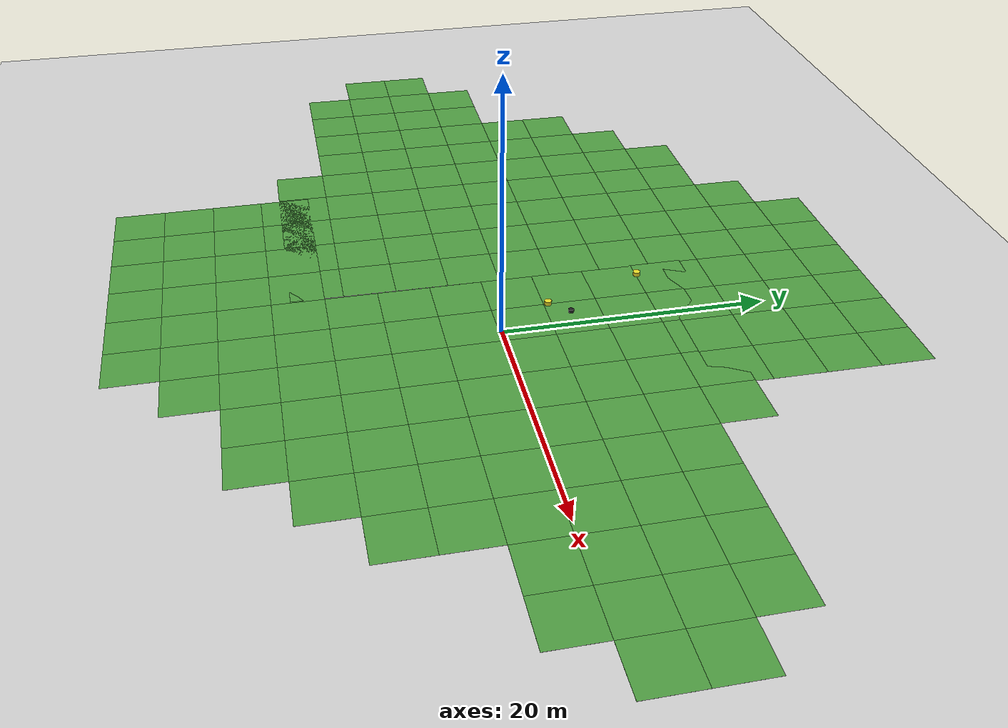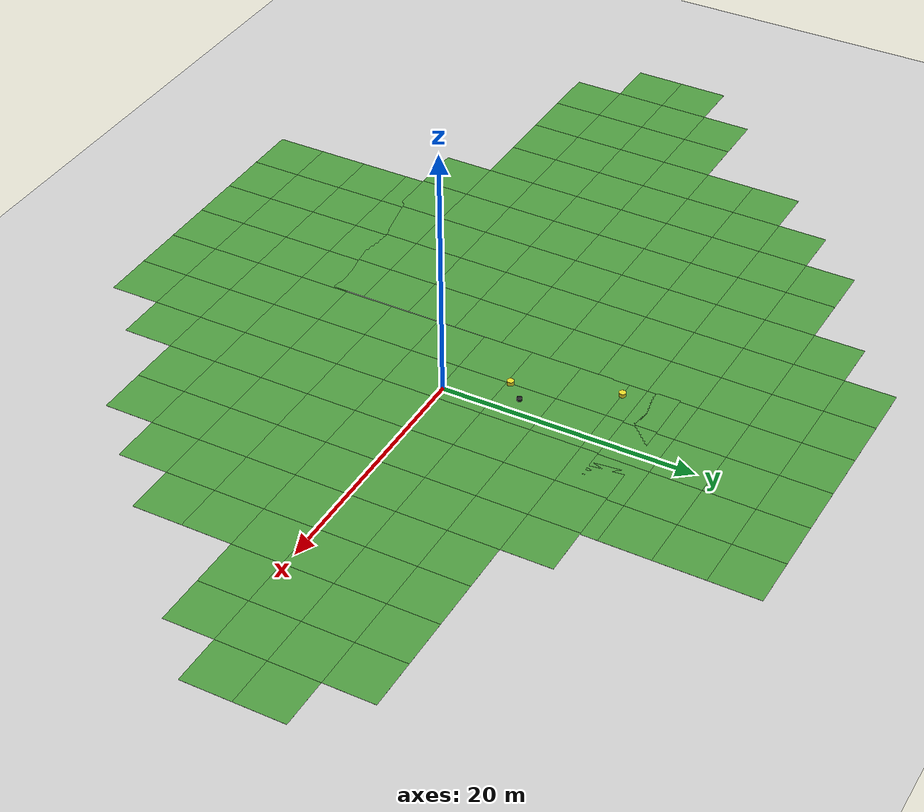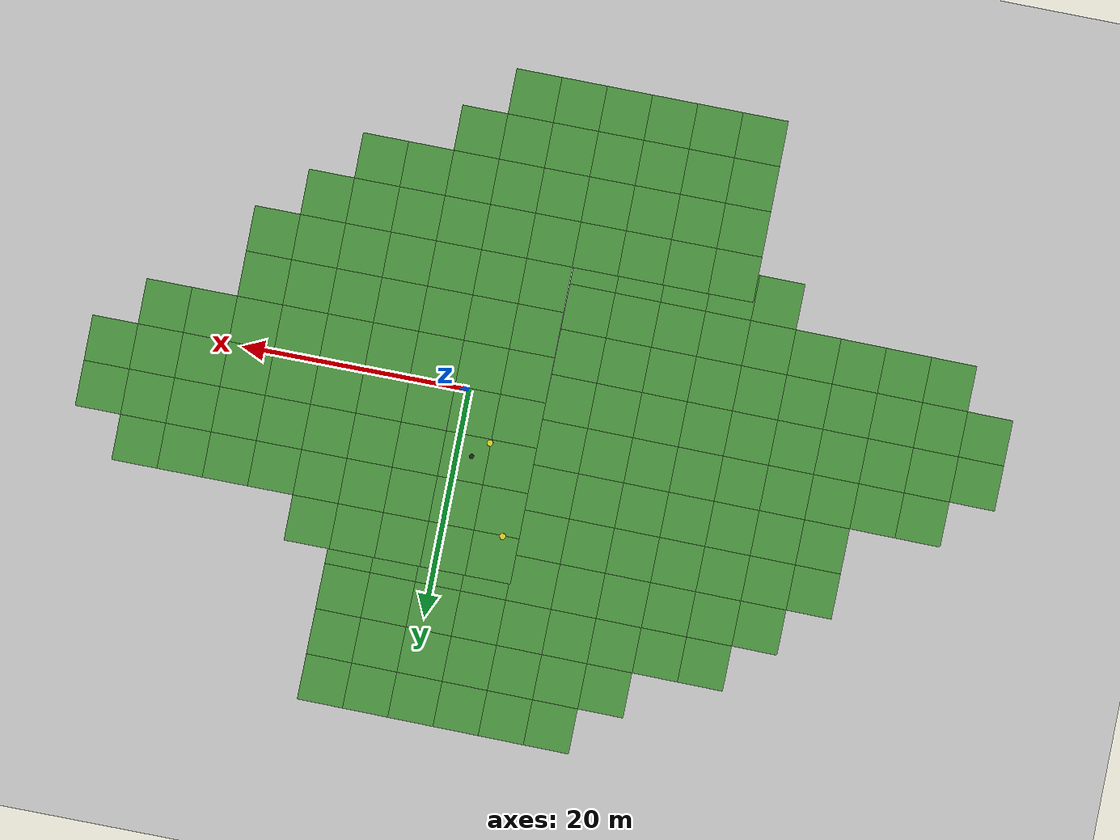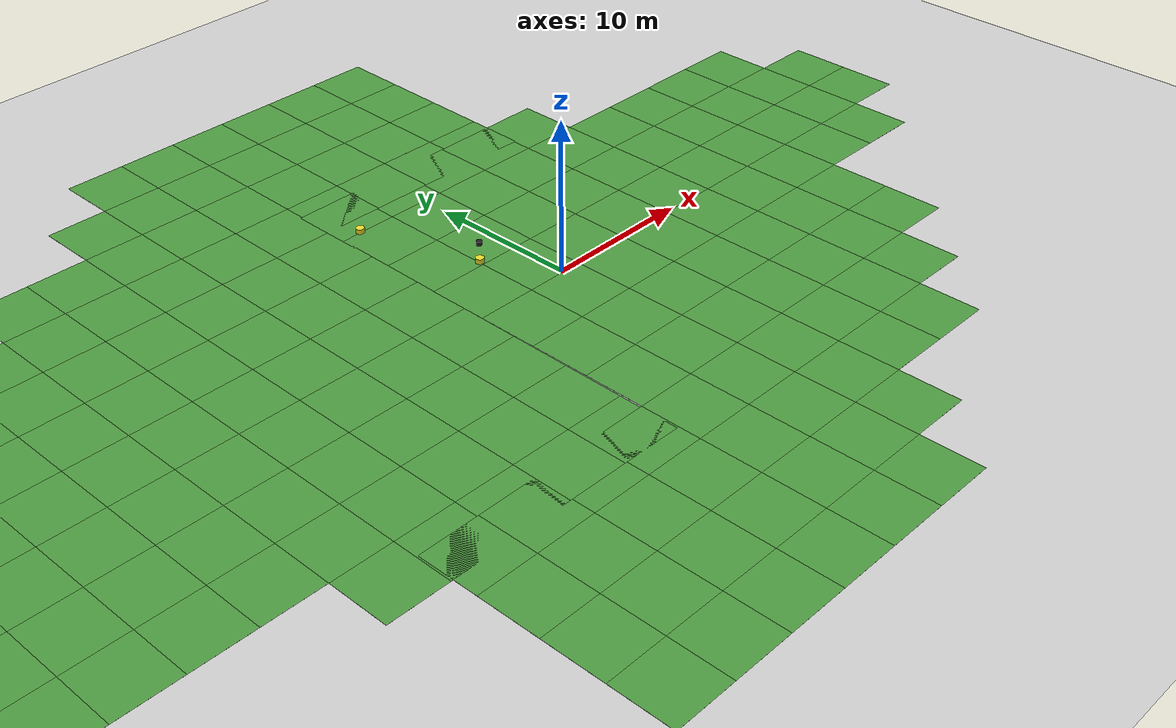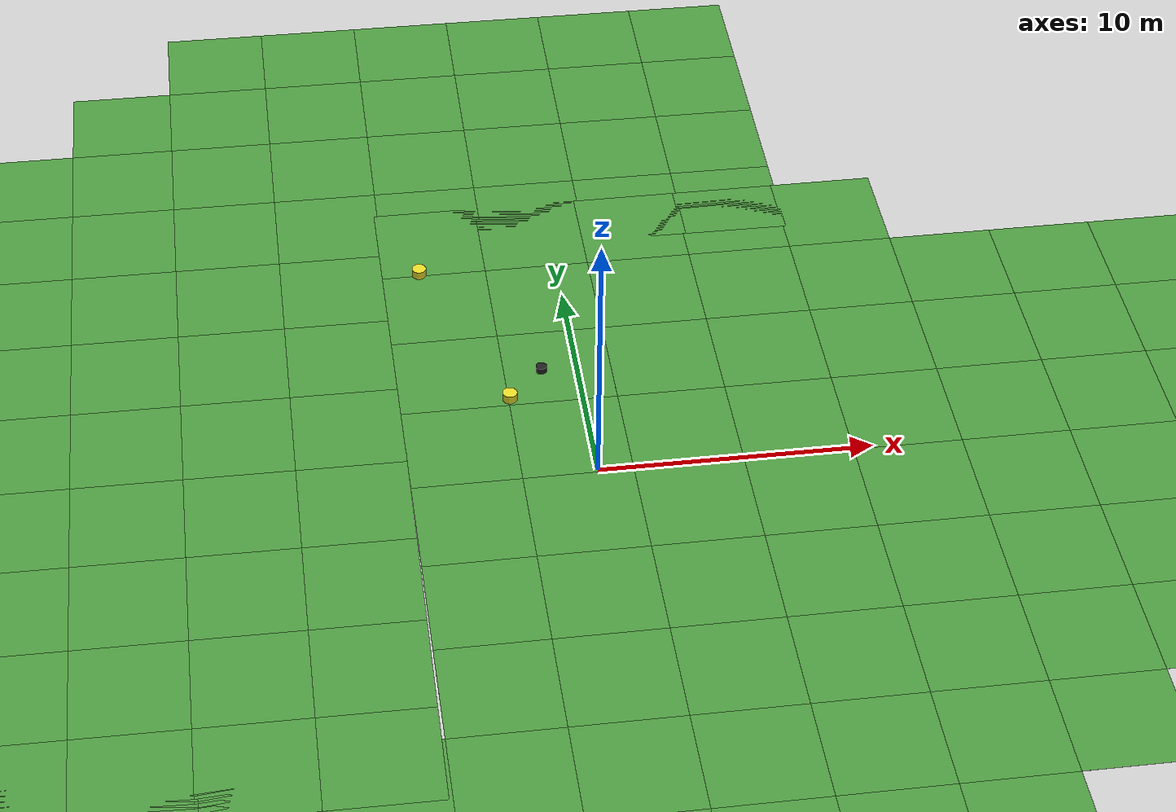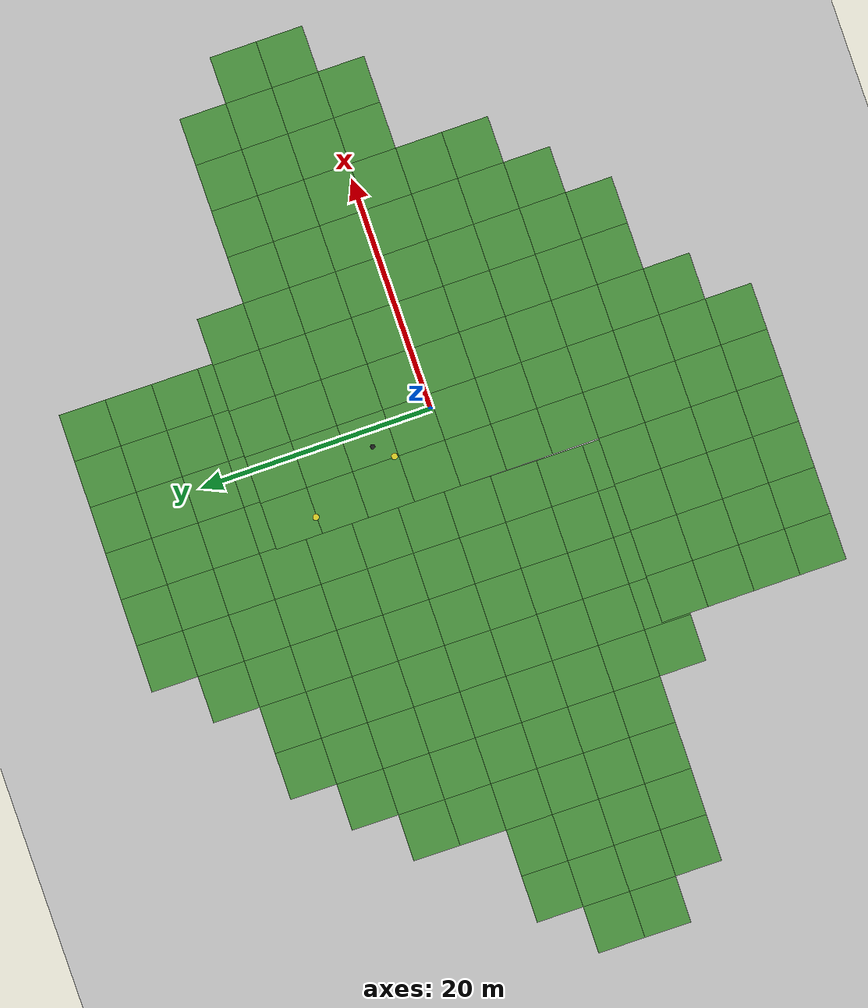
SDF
<sdf version="1.7">
 <world name="default">
  <light name="sun" type="directional">
   <pose>0 0 10 0 -0 0</pose>
   <diffuse>0.8 0.8 0.8 1</diffuse>
   <specular>0.2 0.2 0.2 1</specular>
   <attenuation>
    <range>1000</range>
    <constant>0.9</constant>
    <linear>0.01</linear>
    <quadratic>0.001</quadratic>
   </attenuation>
   <direction>-0.5 0.1 -0.9</direction>
   <spot><inner_angle>0</inner_angle><outer_angle>0</outer_angle><falloff>0</falloff></spot>
  </light>
  <model name="ground_plane">
   <static>1</static>
   <link name="link">
    <collision name="collision">
     <laser_retro>100</laser_retro>
     <geometry><plane><normal>0 0 1</normal><size>100 100</size></plane></geometry>
     <surface><friction><ode><mu>100</mu><mu2>50</mu2></ode></friction></surface>
    </collision>
    <visual name="visual">
     <laser_retro>100</laser_retro>
     <cast_shadows>0</cast_shadows>
     <geometry><plane><normal>0 0 1</normal><size>100 100</size></plane></geometry>
     <material>
      <script><uri>file://media/materials/scripts/gazebo.material</uri><name>Gazebo/Grey</name></script>
     </material>
    </visual>
   </link>
  </model>
  <gravity>0 0 -9.8</gravity>
  <magnetic_field>6e-06 2.3e-05 -4.2e-05</magnetic_field>
  <atmosphere type="adiabatic"/>
  <physics type="ode">
   <max_step_size>0.001</max_step_size>
   <real_time_factor>1</real_time_factor>
   <real_time_update_rate>1000</real_time_update_rate>
  </physics>
  <scene><ambient>0.4 0.4 0.4 1</ambient><background>0.7 0.7 0.7 1</background><shadows>1</shadows></scene>
  <audio><device>default</device></audio>
  <spherical_coordinates>
   <surface_model>EARTH_WGS84</surface_model>
   <latitude_deg>0</latitude_deg>
   <longitude_deg>0</longitude_deg>
   <elevation>0</elevation>
   <heading_deg>0</heading_deg>
  </spherical_coordinates>
  <model name="grass_plane">
   <static>1</static>
   <link name="link">
    <collision name="collision">
     <geometry><plane><normal>0 0 1</normal><size>100 100</size></plane></geometry>
     <surface><friction><ode><mu>0.5</mu><mu2>0.5</mu2></ode></friction></surface>
    </collision>
    <visual name="visual_0">
     <pose>-8 -8 0 0 -0 0</pose>
     <cast_shadows>0</cast_shadows>
     <geometry><plane><normal>0 0 1</normal><size>4 4</size></plane></geometry>
     <material>
      <script>
       <uri>model://grass_plane/materials/scripts</uri>
       <uri>model://grass_plane/materials/textures</uri>
       <name>vrc/grass</name>
      </script>
     </material>
    </visual>
    <visual name="visual_1">
     <pose>-4 -8 0 0 -0 0</pose>
     <cast_shadows>0</cast_shadows>
     <geometry><plane><normal>0 0 1</normal><size>4 4</size></plane></geometry>
     <material>
      <script>
       <uri>model://grass_plane/materials/scripts</uri>
       <uri>model://grass_plane/materials/textures</uri>
       <name>vrc/grass</name>
      </script>
     </material>
    </visual>
    <visual name="visual_2">
     <pose>0 -8 0 0 -0 0</pose>
     <cast_shadows>0</cast_shadows>
     <geometry><plane><normal>0 0 1</normal><size>4 4</size></plane></geometry>
     <material>
      <script>
       <uri>model://grass_plane/materials/scripts</uri>
       <uri>model://grass_plane/materials/textures</uri>
       <name>vrc/grass</name>
      </script>
     </material>
    </visual>
    <visual name="visual_3">
     <pose>4 -8 0 0 -0 0</pose>
     <cast_shadows>0</cast_shadows>
     <geometry><plane><normal>0 0 1</normal><size>4 4</size></plane></geometry>
     <material>
      <script>
       <uri>model://grass_plane/materials/scripts</uri>
       <uri>model://grass_plane/materials/textures</uri>
       <name>vrc/grass</name>
      </script>
     </material>
    </visual>
    <visual name="visual_4">
     <pose>8 -8 0 0 -0 0</pose>
     <cast_shadows>0</cast_shadows>
     <geometry><plane><normal>0 0 1</normal><size>4 4</size></plane></geometry>
     <material>
      <script>
       <uri>model://grass_plane/materials/scripts</uri>
       <uri>model://grass_plane/materials/textures</uri>
       <name>vrc/grass</name>
      </script>
     </material>
    </visual>
    <visual name="visual_5">
     <pose>12 -8 0 0 -0 0</pose>
     <cast_shadows>0</cast_shadows>
     <geometry><plane><normal>0 0 1</normal><size>4 4</size></plane></geometry>
     <material>
      <script>
       <uri>model://grass_plane/materials/scripts</uri>
       <uri>model://grass_plane/materials/textures</uri>
       <name>vrc/grass</name>
      </script>
     </material>
    </visual>
    <visual name="visual_6">
     <pose>-8 -4 0 0 -0 0</pose>
     <cast_shadows>0</cast_shadows>
     <geometry><plane><normal>0 0 1</normal><size>4 4</size></plane></geometry>
     <material>
      <script>
       <uri>model://grass_plane/materials/scripts</uri>
       <uri>model://grass_plane/materials/textures</uri>
       <name>vrc/grass</name>
      </script>
     </material>
    </visual>
    <visual name="visual_7">
     <pose>-4 -4 0 0 -0 0</pose>
     <cast_shadows>0</cast_shadows>
     <geometry><plane><normal>0 0 1</normal><size>4 4</size></plane></geometry>
     <material>
      <script>
       <uri>model://grass_plane/materials/scripts</uri>
       <uri>model://grass_plane/materials/textures</uri>
       <name>vrc/grass</name>
      </script>
     </material>
    </visual>
    <visual name="visual_8">
     <pose>0 -4 0 0 -0 0</pose>
     <cast_shadows>0</cast_shadows>
     <geometry><plane><normal>0 0 1</normal><size>4 4</size></plane></geometry>
     <material>
      <script>
       <uri>model://grass_plane/materials/scripts</uri>
       <uri>model://grass_plane/materials/textures</uri>
       <name>vrc/grass</name>
      </script>
     </material>
    </visual>
    <visual name="visual_9">
     <pose>4 -4 0 0 -0 0</pose>
     <cast_shadows>0</cast_shadows>
     <geometry><plane><normal>0 0 1</normal><size>4 4</size></plane></geometry>
     <material>
      <script>
       <uri>model://grass_plane/materials/scripts</uri>
       <uri>model://grass_plane/materials/textures</uri>
       <name>vrc/grass</name>
      </script>
     </material>
    </visual>
    <visual name="visual_10">
     <pose>8 -4 0 0 -0 0</pose>
     <cast_shadows>0</cast_shadows>
     <geometry><plane><normal>0 0 1</normal><size>4 4</size></plane></geometry>
     <material>
      <script>
       <uri>model://grass_plane/materials/scripts</uri>
       <uri>model://grass_plane/materials/textures</uri>
       <name>vrc/grass</name>
      </script>
     </material>
    </visual>
    <visual name="visual_11">
     <pose>12 -4 0 0 -0 0</pose>
     <cast_shadows>0</cast_shadows>
     <geometry><plane><normal>0 0 1</normal><size>4 4</size></plane></geometry>
     <material>
      <script>
       <uri>model://grass_plane/materials/scripts</uri>
       <uri>model://grass_plane/materials/textures</uri>
       <name>vrc/grass</name>
      </script>
     </material>
    </visual>
    <visual name="visual_12">
     <pose>16 -4 0 0 -0 0</pose>
     <cast_shadows>0</cast_shadows>
     <geometry><plane><normal>0 0 1</normal><size>4 4</size></plane></geometry>
     <material>
      <script>
       <uri>model://grass_plane/materials/scripts</uri>
       <uri>model://grass_plane/materials/textures</uri>
       <name>vrc/grass</name>
      </script>
     </material>
    </visual>
    <visual name="visual_13">
     <pose>-8 0 0 0 -0 0</pose>
     <cast_shadows>0</cast_shadows>
     <geometry><plane><normal>0 0 1</normal><size>4 4</size></plane></geometry>
     <material>
      <script>
       <uri>model://grass_plane/materials/scripts</uri>
       <uri>model://grass_plane/materials/textures</uri>
       <name>vrc/grass</name>
      </script>
     </material>
    </visual>
    <visual name="visual_14">
     <pose>-4 0 0 0 -0 0</pose>
     <cast_shadows>0</cast_shadows>
     <geometry><plane><normal>0 0 1</normal><size>4 4</size></plane></geometry>
     <material>
      <script>
       <uri>model://grass_plane/materials/scripts</uri>
       <uri>model://grass_plane/materials/textures</uri>
       <name>vrc/grass</name>
      </script>
     </material>
    </visual>
    <visual name="visual_15">
     <cast_shadows>0</cast_shadows>
     <geometry><plane><normal>0 0 1</normal><size>4 4</size></plane></geometry>
     <material>
      <script>
       <uri>model://grass_plane/materials/scripts</uri>
       <uri>model://grass_plane/materials/textures</uri>
       <name>vrc/grass</name>
      </script>
     </material>
    </visual>
    <visual name="visual_16">
     <pose>4 0 0 0 -0 0</pose>
     <cast_shadows>0</cast_shadows>
     <geometry><plane><normal>0 0 1</normal><size>4 4</size></plane></geometry>
     <material>
      <script>
       <uri>model://grass_plane/materials/scripts</uri>
       <uri>model://grass_plane/materials/textures</uri>
       <name>vrc/grass</name>
      </script>
     </material>
    </visual>
    <visual name="visual_17">
     <pose>8 0 0 0 -0 0</pose>
     <cast_shadows>0</cast_shadows>
     <geometry><plane><normal>0 0 1</normal><size>4 4</size></plane></geometry>
     <material>
      <script>
       <uri>model://grass_plane/materials/scripts</uri>
       <uri>model://grass_plane/materials/textures</uri>
       <name>vrc/grass</name>
      </script>
     </material>
    </visual>
    <visual name="visual_18">
     <pose>12 0 0 0 -0 0</pose>
     <cast_shadows>0</cast_shadows>
     <geometry><plane><normal>0 0 1</normal><size>4 4</size></plane></geometry>
     <material>
      <script>
       <uri>model://grass_plane/materials/scripts</uri>
       <uri>model://grass_plane/materials/textures</uri>
       <name>vrc/grass</name>
      </script>
     </material>
    </visual>
    <visual name="visual_19">
     <pose>16 0 0 0 -0 0</pose>
     <cast_shadows>0</cast_shadows>
     <geometry><plane><normal>0 0 1</normal><size>4 4</size></plane></geometry>
     <material>
      <script>
       <uri>model://grass_plane/materials/scripts</uri>
       <uri>model://grass_plane/materials/textures</uri>
       <name>vrc/grass</name>
      </script>
     </material>
    </visual>
    <visual name="visual_20">
     <pose>20 0 0 0 -0 0</pose>
     <cast_shadows>0</cast_shadows>
     <geometry><plane><normal>0 0 1</normal><size>4 4</size></plane></geometry>
     <material>
      <script>
       <uri>model://grass_plane/materials/scripts</uri>
       <uri>model://grass_plane/materials/textures</uri>
       <name>vrc/grass</name>
      </script>
     </material>
    </visual>
    <visual name="visual_21">
     <pose>24 0 0 0 -0 0</pose>
     <cast_shadows>0</cast_shadows>
     <geometry><plane><normal>0 0 1</normal><size>4 4</size></plane></geometry>
     <material>
      <script>
       <uri>model://grass_plane/materials/scripts</uri>
       <uri>model://grass_plane/materials/textures</uri>
       <name>vrc/grass</name>
      </script>
     </material>
    </visual>
    <visual name="visual_22">
     <pose>-8 4 0 0 -0 0</pose>
     <cast_shadows>0</cast_shadows>
     <geometry><plane><normal>0 0 1</normal><size>4 4</size></plane></geometry>
     <material>
      <script>
       <uri>model://grass_plane/materials/scripts</uri>
       <uri>model://grass_plane/materials/textures</uri>
       <name>vrc/grass</name>
      </script>
     </material>
    </visual>
    <visual name="visual_23">
     <pose>-4 4 0 0 -0 0</pose>
     <cast_shadows>0</cast_shadows>
     <geometry><plane><normal>0 0 1</normal><size>4 4</size></plane></geometry>
     <material>
      <script>
       <uri>model://grass_plane/materials/scripts</uri>
       <uri>model://grass_plane/materials/textures</uri>
       <name>vrc/grass</name>
      </script>
     </material>
    </visual>
    <visual name="visual_24">
     <pose>0 4 0 0 -0 0</pose>
     <cast_shadows>0</cast_shadows>
     <geometry><plane><normal>0 0 1</normal><size>4 4</size></plane></geometry>
     <material>
      <script>
       <uri>model://grass_plane/materials/scripts</uri>
       <uri>model://grass_plane/materials/textures</uri>
       <name>vrc/grass</name>
      </script>
     </material>
    </visual>
    <visual name="visual_25">
     <pose>4 4 0 0 -0 0</pose>
     <cast_shadows>0</cast_shadows>
     <geometry><plane><normal>0 0 1</normal><size>4 4</size></plane></geometry>
     <material>
      <script>
       <uri>model://grass_plane/materials/scripts</uri>
       <uri>model://grass_plane/materials/textures</uri>
       <name>vrc/grass</name>
      </script>
     </material>
    </visual>
    <visual name="visual_26">
     <pose>8 4 0 0 -0 0</pose>
     <cast_shadows>0</cast_shadows>
     <geometry><plane><normal>0 0 1</normal><size>4 4</size></plane></geometry>
     <material>
      <script>
       <uri>model://grass_plane/materials/scripts</uri>
       <uri>model://grass_plane/materials/textures</uri>
       <name>vrc/grass</name>
      </script>
     </material>
    </visual>
    <visual name="visual_27">
     <pose>12 4 0 0 -0 0</pose>
     <cast_shadows>0</cast_shadows>
     <geometry><plane><normal>0 0 1</normal><size>4 4</size></plane></geometry>
     <material>
      <script>
       <uri>model://grass_plane/materials/scripts</uri>
       <uri>model://grass_plane/materials/textures</uri>
       <name>vrc/grass</name>
      </script>
     </material>
    </visual>
    <visual name="visual_28">
     <pose>16 4 0 0 -0 0</pose>
     <cast_shadows>0</cast_shadows>
     <geometry><plane><normal>0 0 1</normal><size>4 4</size></plane></geometry>
     <material>
      <script>
       <uri>model://grass_plane/materials/scripts</uri>
       <uri>model://grass_plane/materials/textures</uri>
       <name>vrc/grass</name>
      </script>
     </material>
    </visual>
    <visual name="visual_29">
     <pose>20 4 0 0 -0 0</pose>
     <cast_shadows>0</cast_shadows>
     <geometry><plane><normal>0 0 1</normal><size>4 4</size></plane></geometry>
     <material>
      <script>
       <uri>model://grass_plane/materials/scripts</uri>
       <uri>model://grass_plane/materials/textures</uri>
       <name>vrc/grass</name>
      </script>
     </material>
    </visual>
    <visual name="visual_30">
     <pose>24 4 0 0 -0 0</pose>
     <cast_shadows>0</cast_shadows>
     <geometry><plane><normal>0 0 1</normal><size>4 4</size></plane></geometry>
     <material>
      <script>
       <uri>model://grass_plane/materials/scripts</uri>
       <uri>model://grass_plane/materials/textures</uri>
       <name>vrc/grass</name>
      </script>
     </material>
    </visual>
    <visual name="visual_31">
     <pose>28 4 0 0 -0 0</pose>
     <cast_shadows>0</cast_shadows>
     <geometry><plane><normal>0 0 1</normal><size>4 4</size></plane></geometry>
     <material>
      <script>
       <uri>model://grass_plane/materials/scripts</uri>
       <uri>model://grass_plane/materials/textures</uri>
       <name>vrc/grass</name>
      </script>
     </material>
    </visual>
    <visual name="visual_32">
     <pose>8 8 0 0 -0 0</pose>
     <cast_shadows>0</cast_shadows>
     <geometry><plane><normal>0 0 1</normal><size>4 4</size></plane></geometry>
     <material>
      <script>
       <uri>model://grass_plane/materials/scripts</uri>
       <uri>model://grass_plane/materials/textures</uri>
       <name>vrc/grass</name>
      </script>
     </material>
    </visual>
    <visual name="visual_33">
     <pose>12 8 0 0 -0 0</pose>
     <cast_shadows>0</cast_shadows>
     <geometry><plane><normal>0 0 1</normal><size>4 4</size></plane></geometry>
     <material>
      <script>
       <uri>model://grass_plane/materials/scripts</uri>
       <uri>model://grass_plane/materials/textures</uri>
       <name>vrc/grass</name>
      </script>
     </material>
    </visual>
    <visual name="visual_34">
     <pose>16 8 0 0 -0 0</pose>
     <cast_shadows>0</cast_shadows>
     <geometry><plane><normal>0 0 1</normal><size>4 4</size></plane></geometry>
     <material>
      <script>
       <uri>model://grass_plane/materials/scripts</uri>
       <uri>model://grass_plane/materials/textures</uri>
       <name>vrc/grass</name>
      </script>
     </material>
    </visual>
    <visual name="visual_35">
     <pose>20 8 0 0 -0 0</pose>
     <cast_shadows>0</cast_shadows>
     <geometry><plane><normal>0 0 1</normal><size>4 4</size></plane></geometry>
     <material>
      <script>
       <uri>model://grass_plane/materials/scripts</uri>
       <uri>model://grass_plane/materials/textures</uri>
       <name>vrc/grass</name>
      </script>
     </material>
    </visual>
    <visual name="visual_36">
     <pose>24 8 0 0 -0 0</pose>
     <cast_shadows>0</cast_shadows>
     <geometry><plane><normal>0 0 1</normal><size>4 4</size></plane></geometry>
     <material>
      <script>
       <uri>model://grass_plane/materials/scripts</uri>
       <uri>model://grass_plane/materials/textures</uri>
       <name>vrc/grass</name>
      </script>
     </material>
    </visual>
    <visual name="visual_37">
     <pose>28 8 0 0 -0 0</pose>
     <cast_shadows>0</cast_shadows>
     <geometry><plane><normal>0 0 1</normal><size>4 4</size></plane></geometry>
     <material>
      <script>
       <uri>model://grass_plane/materials/scripts</uri>
       <uri>model://grass_plane/materials/textures</uri>
       <name>vrc/grass</name>
      </script>
     </material>
    </visual>
    <visual name="visual_38">
     <pose>32 8 0 0 -0 0</pose>
     <cast_shadows>0</cast_shadows>
     <geometry><plane><normal>0 0 1</normal><size>4 4</size></plane></geometry>
     <material>
      <script>
       <uri>model://grass_plane/materials/scripts</uri>
       <uri>model://grass_plane/materials/textures</uri>
       <name>vrc/grass</name>
      </script>
     </material>
    </visual>
    <visual name="visual_39">
     <pose>8 12 0 0 -0 0</pose>
     <cast_shadows>0</cast_shadows>
     <geometry><plane><normal>0 0 1</normal><size>4 4</size></plane></geometry>
     <material>
      <script>
       <uri>model://grass_plane/materials/scripts</uri>
       <uri>model://grass_plane/materials/textures</uri>
       <name>vrc/grass</name>
      </script>
     </material>
    </visual>
    <visual name="visual_40">
     <pose>12 12 0 0 -0 0</pose>
     <cast_shadows>0</cast_shadows>
     <geometry><plane><normal>0 0 1</normal><size>4 4</size></plane></geometry>
     <material>
      <script>
       <uri>model://grass_plane/materials/scripts</uri>
       <uri>model://grass_plane/materials/textures</uri>
       <name>vrc/grass</name>
      </script>
     </material>
    </visual>
    <visual name="visual_41">
     <pose>16 12 0 0 -0 0</pose>
     <cast_shadows>0</cast_shadows>
     <geometry><plane><normal>0 0 1</normal><size>4 4</size></plane></geometry>
     <material>
      <script>
       <uri>model://grass_plane/materials/scripts</uri>
       <uri>model://grass_plane/materials/textures</uri>
       <name>vrc/grass</name>
      </script>
     </material>
    </visual>
    <visual name="visual_42">
     <pose>20 12 0 0 -0 0</pose>
     <cast_shadows>0</cast_shadows>
     <geometry><plane><normal>0 0 1</normal><size>4 4</size></plane></geometry>
     <material>
      <script>
       <uri>model://grass_plane/materials/scripts</uri>
       <uri>model://grass_plane/materials/textures</uri>
       <name>vrc/grass</name>
      </script>
     </material>
    </visual>
    <visual name="visual_43">
     <pose>24 12 0 0 -0 0</pose>
     <cast_shadows>0</cast_shadows>
     <geometry><plane><normal>0 0 1</normal><size>4 4</size></plane></geometry>
     <material>
      <script>
       <uri>model://grass_plane/materials/scripts</uri>
       <uri>model://grass_plane/materials/textures</uri>
       <name>vrc/grass</name>
      </script>
     </material>
    </visual>
    <visual name="visual_44">
     <pose>28 12 0 0 -0 0</pose>
     <cast_shadows>0</cast_shadows>
     <geometry><plane><normal>0 0 1</normal><size>4 4</size></plane></geometry>
     <material>
      <script>
       <uri>model://grass_plane/materials/scripts</uri>
       <uri>model://grass_plane/materials/textures</uri>
       <name>vrc/grass</name>
      </script>
     </material>
    </visual>
    <visual name="visual_45">
     <pose>32 12 0 0 -0 0</pose>
     <cast_shadows>0</cast_shadows>
     <geometry><plane><normal>0 0 1</normal><size>4 4</size></plane></geometry>
     <material>
      <script>
       <uri>model://grass_plane/materials/scripts</uri>
       <uri>model://grass_plane/materials/textures</uri>
       <name>vrc/grass</name>
      </script>
     </material>
    </visual>
    <visual name="visual_46">
     <pose>8 16 0 0 -0 0</pose>
     <cast_shadows>0</cast_shadows>
     <geometry><plane><normal>0 0 1</normal><size>4 4</size></plane></geometry>
     <material>
      <script>
       <uri>model://grass_plane/materials/scripts</uri>
       <uri>model://grass_plane/materials/textures</uri>
       <name>vrc/grass</name>
      </script>
     </material>
    </visual>
    <visual name="visual_47">
     <pose>12 16 0 0 -0 0</pose>
     <cast_shadows>0</cast_shadows>
     <geometry><plane><normal>0 0 1</normal><size>4 4</size></plane></geometry>
     <material>
      <script>
       <uri>model://grass_plane/materials/scripts</uri>
       <uri>model://grass_plane/materials/textures</uri>
       <name>vrc/grass</name>
      </script>
     </material>
    </visual>
    <visual name="visual_48">
     <pose>16 16 0 0 -0 0</pose>
     <cast_shadows>0</cast_shadows>
     <geometry><plane><normal>0 0 1</normal><size>4 4</size></plane></geometry>
     <material>
      <script>
       <uri>model://grass_plane/materials/scripts</uri>
       <uri>model://grass_plane/materials/textures</uri>
       <name>vrc/grass</name>
      </script>
     </material>
    </visual>
    <visual name="visual_49">
     <pose>20 16 0 0 -0 0</pose>
     <cast_shadows>0</cast_shadows>
     <geometry><plane><normal>0 0 1</normal><size>4 4</size></plane></geometry>
     <material>
      <script>
       <uri>model://grass_plane/materials/scripts</uri>
       <uri>model://grass_plane/materials/textures</uri>
       <name>vrc/grass</name>
      </script>
     </material>
    </visual>
    <visual name="visual_50">
     <pose>24 16 0 0 -0 0</pose>
     <cast_shadows>0</cast_shadows>
     <geometry><plane><normal>0 0 1</normal><size>4 4</size></plane></geometry>
     <material>
      <script>
       <uri>model://grass_plane/materials/scripts</uri>
       <uri>model://grass_plane/materials/textures</uri>
       <name>vrc/grass</name>
      </script>
     </material>
    </visual>
    <visual name="visual_51">
     <pose>28 16 0 0 -0 0</pose>
     <cast_shadows>0</cast_shadows>
     <geometry><plane><normal>0 0 1</normal><size>4 4</size></plane></geometry>
     <material>
      <script>
       <uri>model://grass_plane/materials/scripts</uri>
       <uri>model://grass_plane/materials/textures</uri>
       <name>vrc/grass</name>
      </script>
     </material>
    </visual>
    <visual name="visual_52">
     <pose>32 16 0 0 -0 0</pose>
     <cast_shadows>0</cast_shadows>
     <geometry><plane><normal>0 0 1</normal><size>4 4</size></plane></geometry>
     <material>
      <script>
       <uri>model://grass_plane/materials/scripts</uri>
       <uri>model://grass_plane/materials/textures</uri>
       <name>vrc/grass</name>
      </script>
     </material>
    </visual>
    <visual name="visual_53">
     <pose>36 16 0 0 -0 0</pose>
     <cast_shadows>0</cast_shadows>
     <geometry><plane><normal>0 0 1</normal><size>4 4</size></plane></geometry>
     <material>
      <script>
       <uri>model://grass_plane/materials/scripts</uri>
       <uri>model://grass_plane/materials/textures</uri>
       <name>vrc/grass</name>
      </script>
     </material>
    </visual>
    <visual name="visual_54">
     <pose>40 16 0 0 -0 0</pose>
     <cast_shadows>0</cast_shadows>
     <geometry><plane><normal>0 0 1</normal><size>4 4</size></plane></geometry>
     <material>
      <script>
       <uri>model://grass_plane/materials/scripts</uri>
       <uri>model://grass_plane/materials/textures</uri>
       <name>vrc/grass</name>
      </script>
     </material>
    </visual>
    <visual name="visual_55">
     <pose>8 20 0 0 -0 0</pose>
     <cast_shadows>0</cast_shadows>
     <geometry><plane><normal>0 0 1</normal><size>4 4</size></plane></geometry>
     <material>
      <script>
       <uri>model://grass_plane/materials/scripts</uri>
       <uri>model://grass_plane/materials/textures</uri>
       <name>vrc/grass</name>
      </script>
     </material>
    </visual>
    <visual name="visual_56">
     <pose>12 20 0 0 -0 0</pose>
     <cast_shadows>0</cast_shadows>
     <geometry><plane><normal>0 0 1</normal><size>4 4</size></plane></geometry>
     <material>
      <script>
       <uri>model://grass_plane/materials/scripts</uri>
       <uri>model://grass_plane/materials/textures</uri>
       <name>vrc/grass</name>
      </script>
     </material>
    </visual>
    <visual name="visual_57">
     <pose>16 20 0 0 -0 0</pose>
     <cast_shadows>0</cast_shadows>
     <geometry><plane><normal>0 0 1</normal><size>4 4</size></plane></geometry>
     <material>
      <script>
       <uri>model://grass_plane/materials/scripts</uri>
       <uri>model://grass_plane/materials/textures</uri>
       <name>vrc/grass</name>
      </script>
     </material>
    </visual>
    <visual name="visual_58">
     <pose>20 20 0 0 -0 0</pose>
     <cast_shadows>0</cast_shadows>
     <geometry><plane><normal>0 0 1</normal><size>4 4</size></plane></geometry>
     <material>
      <script>
       <uri>model://grass_plane/materials/scripts</uri>
       <uri>model://grass_plane/materials/textures</uri>
       <name>vrc/grass</name>
      </script>
     </material>
    </visual>
    <visual name="visual_59">
     <pose>24 20 0 0 -0 0</pose>
     <cast_shadows>0</cast_shadows>
     <geometry><plane><normal>0 0 1</normal><size>4 4</size></plane></geometry>
     <material>
      <script>
       <uri>model://grass_plane/materials/scripts</uri>
       <uri>model://grass_plane/materials/textures</uri>
       <name>vrc/grass</name>
      </script>
     </material>
    </visual>
    <visual name="visual_60">
     <pose>28 20 0 0 -0 0</pose>
     <cast_shadows>0</cast_shadows>
     <geometry><plane><normal>0 0 1</normal><size>4 4</size></plane></geometry>
     <material>
      <script>
       <uri>model://grass_plane/materials/scripts</uri>
       <uri>model://grass_plane/materials/textures</uri>
       <name>vrc/grass</name>
      </script>
     </material>
    </visual>
    <visual name="visual_61">
     <pose>32 20 0 0 -0 0</pose>
     <cast_shadows>0</cast_shadows>
     <geometry><plane><normal>0 0 1</normal><size>4 4</size></plane></geometry>
     <material>
      <script>
       <uri>model://grass_plane/materials/scripts</uri>
       <uri>model://grass_plane/materials/textures</uri>
       <name>vrc/grass</name>
      </script>
     </material>
    </visual>
    <visual name="visual_62">
     <pose>36 20 0 0 -0 0</pose>
     <cast_shadows>0</cast_shadows>
     <geometry><plane><normal>0 0 1</normal><size>4 4</size></plane></geometry>
     <material>
      <script>
       <uri>model://grass_plane/materials/scripts</uri>
       <uri>model://grass_plane/materials/textures</uri>
       <name>vrc/grass</name>
      </script>
     </material>
    </visual>
    <visual name="visual_63">
     <pose>40 20 0 0 -0 0</pose>
     <cast_shadows>0</cast_shadows>
     <geometry><plane><normal>0 0 1</normal><size>4 4</size></plane></geometry>
     <material>
      <script>
       <uri>model://grass_plane/materials/scripts</uri>
       <uri>model://grass_plane/materials/textures</uri>
       <name>vrc/grass</name>
      </script>
     </material>
    </visual>
    <visual name="visual_63a">
     <pose>44 20 0 0 -0 0</pose>
     <cast_shadows>0</cast_shadows>
     <geometry><plane><normal>0 0 1</normal><size>4 4</size></plane></geometry>
     <material>
      <script>
       <uri>model://grass_plane/materials/scripts</uri>
       <uri>model://grass_plane/materials/textures</uri>
       <name>vrc/grass</name>
      </script>
     </material>
    </visual>
    <visual name="visual_64">
     <pose>8 24 0 0 -0 0</pose>
     <cast_shadows>0</cast_shadows>
     <geometry><plane><normal>0 0 1</normal><size>4 4</size></plane></geometry>
     <material>
      <script>
       <uri>model://grass_plane/materials/scripts</uri>
       <uri>model://grass_plane/materials/textures</uri>
       <name>vrc/grass</name>
      </script>
     </material>
    </visual>
    <visual name="visual_65">
     <pose>12 24 0 0 -0 0</pose>
     <cast_shadows>0</cast_shadows>
     <geometry><plane><normal>0 0 1</normal><size>4 4</size></plane></geometry>
     <material>
      <script>
       <uri>model://grass_plane/materials/scripts</uri>
       <uri>model://grass_plane/materials/textures</uri>
       <name>vrc/grass</name>
      </script>
     </material>
    </visual>
    <visual name="visual_66">
     <pose>16 24 0 0 -0 0</pose>
     <cast_shadows>0</cast_shadows>
     <geometry><plane><normal>0 0 1</normal><size>4 4</size></plane></geometry>
     <material>
      <script>
       <uri>model://grass_plane/materials/scripts</uri>
       <uri>model://grass_plane/materials/textures</uri>
       <name>vrc/grass</name>
      </script>
     </material>
    </visual>
    <visual name="visual_67">
     <pose>20 24 0 0 -0 0</pose>
     <cast_shadows>0</cast_shadows>
     <geometry><plane><normal>0 0 1</normal><size>4 4</size></plane></geometry>
     <material>
      <script>
       <uri>model://grass_plane/materials/scripts</uri>
       <uri>model://grass_plane/materials/textures</uri>
       <name>vrc/grass</name>
      </script>
     </material>
    </visual>
    <visual name="visual_68">
     <pose>24 24 0 0 -0 0</pose>
     <cast_shadows>0</cast_shadows>
     <geometry><plane><normal>0 0 1</normal><size>4 4</size></plane></geometry>
     <material>
      <script>
       <uri>model://grass_plane/materials/scripts</uri>
       <uri>model://grass_plane/materials/textures</uri>
       <name>vrc/grass</name>
      </script>
     </material>
    </visual>
    <visual name="visual_69">
     <pose>28 24 0 0 -0 0</pose>
     <cast_shadows>0</cast_shadows>
     <geometry><plane><normal>0 0 1</normal><size>4 4</size></plane></geometry>
     <material>
      <script>
       <uri>model://grass_plane/materials/scripts</uri>
       <uri>model://grass_plane/materials/textures</uri>
       <name>vrc/grass</name>
      </script>
     </material>
    </visual>
    <visual name="visual_70">
     <pose>32 24 0 0 -0 0</pose>
     <cast_shadows>0</cast_shadows>
     <geometry><plane><normal>0 0 1</normal><size>4 4</size></plane></geometry>
     <material>
      <script>
       <uri>model://grass_plane/materials/scripts</uri>
       <uri>model://grass_plane/materials/textures</uri>
       <name>vrc/grass</name>
      </script>
     </material>
    </visual>
    <visual name="visual_71">
     <pose>36 24 0 0 -0 0</pose>
     <cast_shadows>0</cast_shadows>
     <geometry><plane><normal>0 0 1</normal><size>4 4</size></plane></geometry>
     <material>
      <script>
       <uri>model://grass_plane/materials/scripts</uri>
       <uri>model://grass_plane/materials/textures</uri>
       <name>vrc/grass</name>
      </script>
     </material>
    </visual>
    <visual name="visual_72">
     <pose>40 24 0 0 -0 0</pose>
     <cast_shadows>0</cast_shadows>
     <geometry><plane><normal>0 0 1</normal><size>4 4</size></plane></geometry>
     <material>
      <script>
       <uri>model://grass_plane/materials/scripts</uri>
       <uri>model://grass_plane/materials/textures</uri>
       <name>vrc/grass</name>
      </script>
     </material>
    </visual>
    <visual name="visual_72a">
     <pose>44 24 0 0 -0 0</pose>
     <cast_shadows>0</cast_shadows>
     <geometry><plane><normal>0 0 1</normal><size>4 4</size></plane></geometry>
     <material>
      <script>
       <uri>model://grass_plane/materials/scripts</uri>
       <uri>model://grass_plane/materials/textures</uri>
       <name>vrc/grass</name>
      </script>
     </material>
    </visual>
    <visual name="visual_73">
     <pose>8 28 0 0 -0 0</pose>
     <cast_shadows>0</cast_shadows>
     <geometry><plane><normal>0 0 1</normal><size>4 4</size></plane></geometry>
     <material>
      <script>
       <uri>model://grass_plane/materials/scripts</uri>
       <uri>model://grass_plane/materials/textures</uri>
       <name>vrc/grass</name>
      </script>
     </material>
    </visual>
    <visual name="visual_74">
     <pose>12 28 0 0 -0 0</pose>
     <cast_shadows>0</cast_shadows>
     <geometry><plane><normal>0 0 1</normal><size>4 4</size></plane></geometry>
     <material>
      <script>
       <uri>model://grass_plane/materials/scripts</uri>
       <uri>model://grass_plane/materials/textures</uri>
       <name>vrc/grass</name>
      </script>
     </material>
    </visual>
    <visual name="visual_75">
     <pose>16 28 0 0 -0 0</pose>
     <cast_shadows>0</cast_shadows>
     <geometry><plane><normal>0 0 1</normal><size>4 4</size></plane></geometry>
     <material>
      <script>
       <uri>model://grass_plane/materials/scripts</uri>
       <uri>model://grass_plane/materials/textures</uri>
       <name>vrc/grass</name>
      </script>
     </material>
    </visual>
    <visual name="visual_76">
     <pose>20 28 0 0 -0 0</pose>
     <cast_shadows>0</cast_shadows>
     <geometry><plane><normal>0 0 1</normal><size>4 4</size></plane></geometry>
     <material>
      <script>
       <uri>model://grass_plane/materials/scripts</uri>
       <uri>model://grass_plane/materials/textures</uri>
       <name>vrc/grass</name>
      </script>
     </material>
    </visual>
    <visual name="visual_77">
     <pose>24 28 0 0 -0 0</pose>
     <cast_shadows>0</cast_shadows>
     <geometry><plane><normal>0 0 1</normal><size>4 4</size></plane></geometry>
     <material>
      <script>
       <uri>model://grass_plane/materials/scripts</uri>
       <uri>model://grass_plane/materials/textures</uri>
       <name>vrc/grass</name>
      </script>
     </material>
    </visual>
    <visual name="visual_78">
     <pose>28 28 0 0 -0 0</pose>
     <cast_shadows>0</cast_shadows>
     <geometry><plane><normal>0 0 1</normal><size>4 4</size></plane></geometry>
     <material>
      <script>
       <uri>model://grass_plane/materials/scripts</uri>
       <uri>model://grass_plane/materials/textures</uri>
       <name>vrc/grass</name>
      </script>
     </material>
    </visual>
    <visual name="visual_79">
     <pose>32 28 0 0 -0 0</pose>
     <cast_shadows>0</cast_shadows>
     <geometry><plane><normal>0 0 1</normal><size>4 4</size></plane></geometry>
     <material>
      <script>
       <uri>model://grass_plane/materials/scripts</uri>
       <uri>model://grass_plane/materials/textures</uri>
       <name>vrc/grass</name>
      </script>
     </material>
    </visual>
    <visual name="visual_80">
     <pose>36 28 0 0 -0 0</pose>
     <cast_shadows>0</cast_shadows>
     <geometry><plane><normal>0 0 1</normal><size>4 4</size></plane></geometry>
     <material>
      <script>
       <uri>model://grass_plane/materials/scripts</uri>
       <uri>model://grass_plane/materials/textures</uri>
       <name>vrc/grass</name>
      </script>
     </material>
    </visual>
    <visual name="visual_81">
     <pose>40 28 0 0 -0 0</pose>
     <cast_shadows>0</cast_shadows>
     <geometry><plane><normal>0 0 1</normal><size>4 4</size></plane></geometry>
     <material>
      <script>
       <uri>model://grass_plane/materials/scripts</uri>
       <uri>model://grass_plane/materials/textures</uri>
       <name>vrc/grass</name>
      </script>
     </material>
    </visual>
    <visual name="visual_82">
     <pose>8 32 0 0 -0 0</pose>
     <cast_shadows>0</cast_shadows>
     <geometry><plane><normal>0 0 1</normal><size>4 4</size></plane></geometry>
     <material>
      <script>
       <uri>model://grass_plane/materials/scripts</uri>
       <uri>model://grass_plane/materials/textures</uri>
       <name>vrc/grass</name>
      </script>
     </material>
    </visual>
    <visual name="visual_83">
     <pose>12 32 0 0 -0 0</pose>
     <cast_shadows>0</cast_shadows>
     <geometry><plane><normal>0 0 1</normal><size>4 4</size></plane></geometry>
     <material>
      <script>
       <uri>model://grass_plane/materials/scripts</uri>
       <uri>model://grass_plane/materials/textures</uri>
       <name>vrc/grass</name>
      </script>
     </material>
    </visual>
    <visual name="visual_84">
     <pose>16 32 0 0 -0 0</pose>
     <cast_shadows>0</cast_shadows>
     <geometry><plane><normal>0 0 1</normal><size>4 4</size></plane></geometry>
     <material>
      <script>
       <uri>model://grass_plane/materials/scripts</uri>
       <uri>model://grass_plane/materials/textures</uri>
       <name>vrc/grass</name>
      </script>
     </material>
    </visual>
    <visual name="visual_85">
     <pose>20 32 0 0 -0 0</pose>
     <cast_shadows>0</cast_shadows>
     <geometry><plane><normal>0 0 1</normal><size>4 4</size></plane></geometry>
     <material>
      <script>
       <uri>model://grass_plane/materials/scripts</uri>
       <uri>model://grass_plane/materials/textures</uri>
       <name>vrc/grass</name>
      </script>
     </material>
    </visual>
    <visual name="visual_86">
     <pose>24 32 0 0 -0 0</pose>
     <cast_shadows>0</cast_shadows>
     <geometry><plane><normal>0 0 1</normal><size>4 4</size></plane></geometry>
     <material>
      <script>
       <uri>model://grass_plane/materials/scripts</uri>
       <uri>model://grass_plane/materials/textures</uri>
       <name>vrc/grass</name>
      </script>
     </material>
    </visual>
   </link>
   <pose>-12.7617 -18.2154 0.1 0 -0 0</pose>
  </model>
  <model name="grass_plane_0">
   <static>1</static>
   <link name="link">
    <collision name="collision">
     <geometry><plane><normal>0 0 1</normal><size>100 100</size></plane></geometry>
     <surface><friction><ode><mu>0.5</mu><mu2>0.5</mu2></ode></friction></surface>
    </collision>
    <visual name="visual_0">
     <pose>-8 -8 0 0 -0 0</pose>
     <cast_shadows>0</cast_shadows>
     <geometry><plane><normal>0 0 1</normal><size>4 4</size></plane></geometry>
     <material>
      <script>
       <uri>model://grass_plane/materials/scripts</uri>
       <uri>model://grass_plane/materials/textures</uri>
       <name>vrc/grass</name>
      </script>
     </material>
    </visual>
    <visual name="visual_1">
     <pose>-4 -8 0 0 -0 0</pose>
     <cast_shadows>0</cast_shadows>
     <geometry><plane><normal>0 0 1</normal><size>4 4</size></plane></geometry>
     <material>
      <script>
       <uri>model://grass_plane/materials/scripts</uri>
       <uri>model://grass_plane/materials/textures</uri>
       <name>vrc/grass</name>
      </script>
     </material>
    </visual>
    <visual name="visual_2">
     <pose>0 -8 0 0 -0 0</pose>
     <cast_shadows>0</cast_shadows>
     <geometry><plane><normal>0 0 1</normal><size>4 4</size></plane></geometry>
     <material>
      <script>
       <uri>model://grass_plane/materials/scripts</uri>
       <uri>model://grass_plane/materials/textures</uri>
       <name>vrc/grass</name>
      </script>
     </material>
    </visual>
    <visual name="visual_3">
     <pose>4 -8 0 0 -0 0</pose>
     <cast_shadows>0</cast_shadows>
     <geometry><plane><normal>0 0 1</normal><size>4 4</size></plane></geometry>
     <material>
      <script>
       <uri>model://grass_plane/materials/scripts</uri>
       <uri>model://grass_plane/materials/textures</uri>
       <name>vrc/grass</name>
      </script>
     </material>
    </visual>
    <visual name="visual_4">
     <pose>8 -8 0 0 -0 0</pose>
     <cast_shadows>0</cast_shadows>
     <geometry><plane><normal>0 0 1</normal><size>4 4</size></plane></geometry>
     <material>
      <script>
       <uri>model://grass_plane/materials/scripts</uri>
       <uri>model://grass_plane/materials/textures</uri>
       <name>vrc/grass</name>
      </script>
     </material>
    </visual>
    <visual name="visual_5">
     <pose>12 -8 0 0 -0 0</pose>
     <cast_shadows>0</cast_shadows>
     <geometry><plane><normal>0 0 1</normal><size>4 4</size></plane></geometry>
     <material>
      <script>
       <uri>model://grass_plane/materials/scripts</uri>
       <uri>model://grass_plane/materials/textures</uri>
       <name>vrc/grass</name>
      </script>
     </material>
    </visual>
    <visual name="visual_6">
     <pose>-8 -4 0 0 -0 0</pose>
     <cast_shadows>0</cast_shadows>
     <geometry><plane><normal>0 0 1</normal><size>4 4</size></plane></geometry>
     <material>
      <script>
       <uri>model://grass_plane/materials/scripts</uri>
       <uri>model://grass_plane/materials/textures</uri>
       <name>vrc/grass</name>
      </script>
     </material>
    </visual>
    <visual name="visual_7">
     <pose>-4 -4 0 0 -0 0</pose>
     <cast_shadows>0</cast_shadows>
     <geometry><plane><normal>0 0 1</normal><size>4 4</size></plane></geometry>
     <material>
      <script>
       <uri>model://grass_plane/materials/scripts</uri>
       <uri>model://grass_plane/materials/textures</uri>
       <name>vrc/grass</name>
      </script>
     </material>
    </visual>
    <visual name="visual_8">
     <pose>0 -4 0 0 -0 0</pose>
     <cast_shadows>0</cast_shadows>
     <geometry><plane><normal>0 0 1</normal><size>4 4</size></plane></geometry>
     <material>
      <script>
       <uri>model://grass_plane/materials/scripts</uri>
       <uri>model://grass_plane/materials/textures</uri>
       <name>vrc/grass</name>
      </script>
     </material>
    </visual>
    <visual name="visual_9">
     <pose>4 -4 0 0 -0 0</pose>
     <cast_shadows>0</cast_shadows>
     <geometry><plane><normal>0 0 1</normal><size>4 4</size></plane></geometry>
     <material>
      <script>
       <uri>model://grass_plane/materials/scripts</uri>
       <uri>model://grass_plane/materials/textures</uri>
       <name>vrc/grass</name>
      </script>
     </material>
    </visual>
    <visual name="visual_10">
     <pose>8 -4 0 0 -0 0</pose>
     <cast_shadows>0</cast_shadows>
     <geometry><plane><normal>0 0 1</normal><size>4 4</size></plane></geometry>
     <material>
      <script>
       <uri>model://grass_plane/materials/scripts</uri>
       <uri>model://grass_plane/materials/textures</uri>
       <name>vrc/grass</name>
      </script>
     </material>
    </visual>
    <visual name="visual_11">
     <pose>12 -4 0 0 -0 0</pose>
     <cast_shadows>0</cast_shadows>
     <geometry><plane><normal>0 0 1</normal><size>4 4</size></plane></geometry>
     <material>
      <script>
       <uri>model://grass_plane/materials/scripts</uri>
       <uri>model://grass_plane/materials/textures</uri>
       <name>vrc/grass</name>
      </script>
     </material>
    </visual>
    <visual name="visual_12">
     <pose>16 -4 0 0 -0 0</pose>
     <cast_shadows>0</cast_shadows>
     <geometry><plane><normal>0 0 1</normal><size>4 4</size></plane></geometry>
     <material>
      <script>
       <uri>model://grass_plane/materials/scripts</uri>
       <uri>model://grass_plane/materials/textures</uri>
       <name>vrc/grass</name>
      </script>
     </material>
    </visual>
    <visual name="visual_13">
     <pose>-8 0 0 0 -0 0</pose>
     <cast_shadows>0</cast_shadows>
     <geometry><plane><normal>0 0 1</normal><size>4 4</size></plane></geometry>
     <material>
      <script>
       <uri>model://grass_plane/materials/scripts</uri>
       <uri>model://grass_plane/materials/textures</uri>
       <name>vrc/grass</name>
      </script>
     </material>
    </visual>
    <visual name="visual_14">
     <pose>-4 0 0 0 -0 0</pose>
     <cast_shadows>0</cast_shadows>
     <geometry><plane><normal>0 0 1</normal><size>4 4</size></plane></geometry>
     <material>
      <script>
       <uri>model://grass_plane/materials/scripts</uri>
       <uri>model://grass_plane/materials/textures</uri>
       <name>vrc/grass</name>
      </script>
     </material>
    </visual>
    <visual name="visual_15">
     <cast_shadows>0</cast_shadows>
     <geometry><plane><normal>0 0 1</normal><size>4 4</size></plane></geometry>
     <material>
      <script>
       <uri>model://grass_plane/materials/scripts</uri>
       <uri>model://grass_plane/materials/textures</uri>
       <name>vrc/grass</name>
      </script>
     </material>
    </visual>
    <visual name="visual_16">
     <pose>4 0 0 0 -0 0</pose>
     <cast_shadows>0</cast_shadows>
     <geometry><plane><normal>0 0 1</normal><size>4 4</size></plane></geometry>
     <material>
      <script>
       <uri>model://grass_plane/materials/scripts</uri>
       <uri>model://grass_plane/materials/textures</uri>
       <name>vrc/grass</name>
      </script>
     </material>
    </visual>
    <visual name="visual_17">
     <pose>8 0 0 0 -0 0</pose>
     <cast_shadows>0</cast_shadows>
     <geometry><plane><normal>0 0 1</normal><size>4 4</size></plane></geometry>
     <material>
      <script>
       <uri>model://grass_plane/materials/scripts</uri>
       <uri>model://grass_plane/materials/textures</uri>
       <name>vrc/grass</name>
      </script>
     </material>
    </visual>
    <visual name="visual_18">
     <pose>12 0 0 0 -0 0</pose>
     <cast_shadows>0</cast_shadows>
     <geometry><plane><normal>0 0 1</normal><size>4 4</size></plane></geometry>
     <material>
      <script>
       <uri>model://grass_plane/materials/scripts</uri>
       <uri>model://grass_plane/materials/textures</uri>
       <name>vrc/grass</name>
      </script>
     </material>
    </visual>
    <visual name="visual_19">
     <pose>16 0 0 0 -0 0</pose>
     <cast_shadows>0</cast_shadows>
     <geometry><plane><normal>0 0 1</normal><size>4 4</size></plane></geometry>
     <material>
      <script>
       <uri>model://grass_plane/materials/scripts</uri>
       <uri>model://grass_plane/materials/textures</uri>
       <name>vrc/grass</name>
      </script>
     </material>
    </visual>
    <visual name="visual_20">
     <pose>20 0 0 0 -0 0</pose>
     <cast_shadows>0</cast_shadows>
     <geometry><plane><normal>0 0 1</normal><size>4 4</size></plane></geometry>
     <material>
      <script>
       <uri>model://grass_plane/materials/scripts</uri>
       <uri>model://grass_plane/materials/textures</uri>
       <name>vrc/grass</name>
      </script>
     </material>
    </visual>
    <visual name="visual_21">
     <pose>24 0 0 0 -0 0</pose>
     <cast_shadows>0</cast_shadows>
     <geometry><plane><normal>0 0 1</normal><size>4 4</size></plane></geometry>
     <material>
      <script>
       <uri>model://grass_plane/materials/scripts</uri>
       <uri>model://grass_plane/materials/textures</uri>
       <name>vrc/grass</name>
      </script>
     </material>
    </visual>
    <visual name="visual_22">
     <pose>-8 4 0 0 -0 0</pose>
     <cast_shadows>0</cast_shadows>
     <geometry><plane><normal>0 0 1</normal><size>4 4</size></plane></geometry>
     <material>
      <script>
       <uri>model://grass_plane/materials/scripts</uri>
       <uri>model://grass_plane/materials/textures</uri>
       <name>vrc/grass</name>
      </script>
     </material>
    </visual>
    <visual name="visual_23">
     <pose>-4 4 0 0 -0 0</pose>
     <cast_shadows>0</cast_shadows>
     <geometry><plane><normal>0 0 1</normal><size>4 4</size></plane></geometry>
     <material>
      <script>
       <uri>model://grass_plane/materials/scripts</uri>
       <uri>model://grass_plane/materials/textures</uri>
       <name>vrc/grass</name>
      </script>
     </material>
    </visual>
    <visual name="visual_24">
     <pose>0 4 0 0 -0 0</pose>
     <cast_shadows>0</cast_shadows>
     <geometry><plane><normal>0 0 1</normal><size>4 4</size></plane></geometry>
     <material>
      <script>
       <uri>model://grass_plane/materials/scripts</uri>
       <uri>model://grass_plane/materials/textures</uri>
       <name>vrc/grass</name>
      </script>
     </material>
    </visual>
    <visual name="visual_25">
     <pose>4 4 0 0 -0 0</pose>
     <cast_shadows>0</cast_shadows>
     <geometry><plane><normal>0 0 1</normal><size>4 4</size></plane></geometry>
     <material>
      <script>
       <uri>model://grass_plane/materials/scripts</uri>
       <uri>model://grass_plane/materials/textures</uri>
       <name>vrc/grass</name>
      </script>
     </material>
    </visual>
    <visual name="visual_26">
     <pose>8 4 0 0 -0 0</pose>
     <cast_shadows>0</cast_shadows>
     <geometry><plane><normal>0 0 1</normal><size>4 4</size></plane></geometry>
     <material>
      <script>
       <uri>model://grass_plane/materials/scripts</uri>
       <uri>model://grass_plane/materials/textures</uri>
       <name>vrc/grass</name>
      </script>
     </material>
    </visual>
    <visual name="visual_27">
     <pose>12 4 0 0 -0 0</pose>
     <cast_shadows>0</cast_shadows>
     <geometry><plane><normal>0 0 1</normal><size>4 4</size></plane></geometry>
     <material>
      <script>
       <uri>model://grass_plane/materials/scripts</uri>
       <uri>model://grass_plane/materials/textures</uri>
       <name>vrc/grass</name>
      </script>
     </material>
    </visual>
    <visual name="visual_28">
     <pose>16 4 0 0 -0 0</pose>
     <cast_shadows>0</cast_shadows>
     <geometry><plane><normal>0 0 1</normal><size>4 4</size></plane></geometry>
     <material>
      <script>
       <uri>model://grass_plane/materials/scripts</uri>
       <uri>model://grass_plane/materials/textures</uri>
       <name>vrc/grass</name>
      </script>
     </material>
    </visual>
    <visual name="visual_29">
     <pose>20 4 0 0 -0 0</pose>
     <cast_shadows>0</cast_shadows>
     <geometry><plane><normal>0 0 1</normal><size>4 4</size></plane></geometry>
     <material>
      <script>
       <uri>model://grass_plane/materials/scripts</uri>
       <uri>model://grass_plane/materials/textures</uri>
       <name>vrc/grass</name>
      </script>
     </material>
    </visual>
    <visual name="visual_30">
     <pose>24 4 0 0 -0 0</pose>
     <cast_shadows>0</cast_shadows>
     <geometry><plane><normal>0 0 1</normal><size>4 4</size></plane></geometry>
     <material>
      <script>
       <uri>model://grass_plane/materials/scripts</uri>
       <uri>model://grass_plane/materials/textures</uri>
       <name>vrc/grass</name>
      </script>
     </material>
    </visual>
    <visual name="visual_31">
     <pose>28 4 0 0 -0 0</pose>
     <cast_shadows>0</cast_shadows>
     <geometry><plane><normal>0 0 1</normal><size>4 4</size></plane></geometry>
     <material>
      <script>
       <uri>model://grass_plane/materials/scripts</uri>
       <uri>model://grass_plane/materials/textures</uri>
       <name>vrc/grass</name>
      </script>
     </material>
    </visual>
    <visual name="visual_32">
     <pose>8 8 0 0 -0 0</pose>
     <cast_shadows>0</cast_shadows>
     <geometry><plane><normal>0 0 1</normal><size>4 4</size></plane></geometry>
     <material>
      <script>
       <uri>model://grass_plane/materials/scripts</uri>
       <uri>model://grass_plane/materials/textures</uri>
       <name>vrc/grass</name>
      </script>
     </material>
    </visual>
    <visual name="visual_33">
     <pose>12 8 0 0 -0 0</pose>
     <cast_shadows>0</cast_shadows>
     <geometry><plane><normal>0 0 1</normal><size>4 4</size></plane></geometry>
     <material>
      <script>
       <uri>model://grass_plane/materials/scripts</uri>
       <uri>model://grass_plane/materials/textures</uri>
       <name>vrc/grass</name>
      </script>
     </material>
    </visual>
    <visual name="visual_34">
     <pose>16 8 0 0 -0 0</pose>
     <cast_shadows>0</cast_shadows>
     <geometry><plane><normal>0 0 1</normal><size>4 4</size></plane></geometry>
     <material>
      <script>
       <uri>model://grass_plane/materials/scripts</uri>
       <uri>model://grass_plane/materials/textures</uri>
       <name>vrc/grass</name>
      </script>
     </material>
    </visual>
    <visual name="visual_35">
     <pose>20 8 0 0 -0 0</pose>
     <cast_shadows>0</cast_shadows>
     <geometry><plane><normal>0 0 1</normal><size>4 4</size></plane></geometry>
     <material>
      <script>
       <uri>model://grass_plane/materials/scripts</uri>
       <uri>model://grass_plane/materials/textures</uri>
       <name>vrc/grass</name>
      </script>
     </material>
    </visual>
    <visual name="visual_36">
     <pose>24 8 0 0 -0 0</pose>
     <cast_shadows>0</cast_shadows>
     <geometry><plane><normal>0 0 1</normal><size>4 4</size></plane></geometry>
     <material>
      <script>
       <uri>model://grass_plane/materials/scripts</uri>
       <uri>model://grass_plane/materials/textures</uri>
       <name>vrc/grass</name>
      </script>
     </material>
    </visual>
    <visual name="visual_37">
     <pose>28 8 0 0 -0 0</pose>
     <cast_shadows>0</cast_shadows>
     <geometry><plane><normal>0 0 1</normal><size>4 4</size></plane></geometry>
     <material>
      <script>
       <uri>model://grass_plane/materials/scripts</uri>
       <uri>model://grass_plane/materials/textures</uri>
       <name>vrc/grass</name>
      </script>
     </material>
    </visual>
    <visual name="visual_38">
     <pose>32 8 0 0 -0 0</pose>
     <cast_shadows>0</cast_shadows>
     <geometry><plane><normal>0 0 1</normal><size>4 4</size></plane></geometry>
     <material>
      <script>
       <uri>model://grass_plane/materials/scripts</uri>
       <uri>model://grass_plane/materials/textures</uri>
       <name>vrc/grass</name>
      </script>
     </material>
    </visual>
    <visual name="visual_39">
     <pose>8 12 0 0 -0 0</pose>
     <cast_shadows>0</cast_shadows>
     <geometry><plane><normal>0 0 1</normal><size>4 4</size></plane></geometry>
     <material>
      <script>
       <uri>model://grass_plane/materials/scripts</uri>
       <uri>model://grass_plane/materials/textures</uri>
       <name>vrc/grass</name>
      </script>
     </material>
    </visual>
    <visual name="visual_40">
     <pose>12 12 0 0 -0 0</pose>
     <cast_shadows>0</cast_shadows>
     <geometry><plane><normal>0 0 1</normal><size>4 4</size></plane></geometry>
     <material>
      <script>
       <uri>model://grass_plane/materials/scripts</uri>
       <uri>model://grass_plane/materials/textures</uri>
       <name>vrc/grass</name>
      </script>
     </material>
    </visual>
    <visual name="visual_41">
     <pose>16 12 0 0 -0 0</pose>
     <cast_shadows>0</cast_shadows>
     <geometry><plane><normal>0 0 1</normal><size>4 4</size></plane></geometry>
     <material>
      <script>
       <uri>model://grass_plane/materials/scripts</uri>
       <uri>model://grass_plane/materials/textures</uri>
       <name>vrc/grass</name>
      </script>
     </material>
    </visual>
    <visual name="visual_42">
     <pose>20 12 0 0 -0 0</pose>
     <cast_shadows>0</cast_shadows>
     <geometry><plane><normal>0 0 1</normal><size>4 4</size></plane></geometry>
     <material>
      <script>
       <uri>model://grass_plane/materials/scripts</uri>
       <uri>model://grass_plane/materials/textures</uri>
       <name>vrc/grass</name>
      </script>
     </material>
    </visual>
    <visual name="visual_43">
     <pose>24 12 0 0 -0 0</pose>
     <cast_shadows>0</cast_shadows>
     <geometry><plane><normal>0 0 1</normal><size>4 4</size></plane></geometry>
     <material>
      <script>
       <uri>model://grass_plane/materials/scripts</uri>
       <uri>model://grass_plane/materials/textures</uri>
       <name>vrc/grass</name>
      </script>
     </material>
    </visual>
    <visual name="visual_44">
     <pose>28 12 0 0 -0 0</pose>
     <cast_shadows>0</cast_shadows>
     <geometry><plane><normal>0 0 1</normal><size>4 4</size></plane></geometry>
     <material>
      <script>
       <uri>model://grass_plane/materials/scripts</uri>
       <uri>model://grass_plane/materials/textures</uri>
       <name>vrc/grass</name>
      </script>
     </material>
    </visual>
    <visual name="visual_45">
     <pose>32 12 0 0 -0 0</pose>
     <cast_shadows>0</cast_shadows>
     <geometry><plane><normal>0 0 1</normal><size>4 4</size></plane></geometry>
     <material>
      <script>
       <uri>model://grass_plane/materials/scripts</uri>
       <uri>model://grass_plane/materials/textures</uri>
       <name>vrc/grass</name>
      </script>
     </material>
    </visual>
    <visual name="visual_46">
     <pose>8 16 0 0 -0 0</pose>
     <cast_shadows>0</cast_shadows>
     <geometry><plane><normal>0 0 1</normal><size>4 4</size></plane></geometry>
     <material>
      <script>
       <uri>model://grass_plane/materials/scripts</uri>
       <uri>model://grass_plane/materials/textures</uri>
       <name>vrc/grass</name>
      </script>
     </material>
    </visual>
    <visual name="visual_47">
     <pose>12 16 0 0 -0 0</pose>
     <cast_shadows>0</cast_shadows>
     <geometry><plane><normal>0 0 1</normal><size>4 4</size></plane></geometry>
     <material>
      <script>
       <uri>model://grass_plane/materials/scripts</uri>
       <uri>model://grass_plane/materials/textures</uri>
       <name>vrc/grass</name>
      </script>
     </material>
    </visual>
    <visual name="visual_48">
     <pose>16 16 0 0 -0 0</pose>
     <cast_shadows>0</cast_shadows>
     <geometry><plane><normal>0 0 1</normal><size>4 4</size></plane></geometry>
     <material>
      <script>
       <uri>model://grass_plane/materials/scripts</uri>
       <uri>model://grass_plane/materials/textures</uri>
       <name>vrc/grass</name>
      </script>
     </material>
    </visual>
    <visual name="visual_49">
     <pose>20 16 0 0 -0 0</pose>
     <cast_shadows>0</cast_shadows>
     <geometry><plane><normal>0 0 1</normal><size>4 4</size></plane></geometry>
     <material>
      <script>
       <uri>model://grass_plane/materials/scripts</uri>
       <uri>model://grass_plane/materials/textures</uri>
       <name>vrc/grass</name>
      </script>
     </material>
    </visual>
    <visual name="visual_50">
     <pose>24 16 0 0 -0 0</pose>
     <cast_shadows>0</cast_shadows>
     <geometry><plane><normal>0 0 1</normal><size>4 4</size></plane></geometry>
     <material>
      <script>
       <uri>model://grass_plane/materials/scripts</uri>
       <uri>model://grass_plane/materials/textures</uri>
       <name>vrc/grass</name>
      </script>
     </material>
    </visual>
    <visual name="visual_51">
     <pose>28 16 0 0 -0 0</pose>
     <cast_shadows>0</cast_shadows>
     <geometry><plane><normal>0 0 1</normal><size>4 4</size></plane></geometry>
     <material>
      <script>
       <uri>model://grass_plane/materials/scripts</uri>
       <uri>model://grass_plane/materials/textures</uri>
       <name>vrc/grass</name>
      </script>
     </material>
    </visual>
    <visual name="visual_52">
     <pose>32 16 0 0 -0 0</pose>
     <cast_shadows>0</cast_shadows>
     <geometry><plane><normal>0 0 1</normal><size>4 4</size></plane></geometry>
     <material>
      <script>
       <uri>model://grass_plane/materials/scripts</uri>
       <uri>model://grass_plane/materials/textures</uri>
       <name>vrc/grass</name>
      </script>
     </material>
    </visual>
    <visual name="visual_53">
     <pose>36 16 0 0 -0 0</pose>
     <cast_shadows>0</cast_shadows>
     <geometry><plane><normal>0 0 1</normal><size>4 4</size></plane></geometry>
     <material>
      <script>
       <uri>model://grass_plane/materials/scripts</uri>
       <uri>model://grass_plane/materials/textures</uri>
       <name>vrc/grass</name>
      </script>
     </material>
    </visual>
    <visual name="visual_54">
     <pose>40 16 0 0 -0 0</pose>
     <cast_shadows>0</cast_shadows>
     <geometry><plane><normal>0 0 1</normal><size>4 4</size></plane></geometry>
     <material>
      <script>
       <uri>model://grass_plane/materials/scripts</uri>
       <uri>model://grass_plane/materials/textures</uri>
       <name>vrc/grass</name>
      </script>
     </material>
    </visual>
    <visual name="visual_55">
     <pose>8 20 0 0 -0 0</pose>
     <cast_shadows>0</cast_shadows>
     <geometry><plane><normal>0 0 1</normal><size>4 4</size></plane></geometry>
     <material>
      <script>
       <uri>model://grass_plane/materials/scripts</uri>
       <uri>model://grass_plane/materials/textures</uri>
       <name>vrc/grass</name>
      </script>
     </material>
    </visual>
    <visual name="visual_56">
     <pose>12 20 0 0 -0 0</pose>
     <cast_shadows>0</cast_shadows>
     <geometry><plane><normal>0 0 1</normal><size>4 4</size></plane></geometry>
     <material>
      <script>
       <uri>model://grass_plane/materials/scripts</uri>
       <uri>model://grass_plane/materials/textures</uri>
       <name>vrc/grass</name>
      </script>
     </material>
    </visual>
    <visual name="visual_57">
     <pose>16 20 0 0 -0 0</pose>
     <cast_shadows>0</cast_shadows>
     <geometry><plane><normal>0 0 1</normal><size>4 4</size></plane></geometry>
     <material>
      <script>
       <uri>model://grass_plane/materials/scripts</uri>
       <uri>model://grass_plane/materials/textures</uri>
       <name>vrc/grass</name>
      </script>
     </material>
    </visual>
    <visual name="visual_58">
     <pose>20 20 0 0 -0 0</pose>
     <cast_shadows>0</cast_shadows>
     <geometry><plane><normal>0 0 1</normal><size>4 4</size></plane></geometry>
     <material>
      <script>
       <uri>model://grass_plane/materials/scripts</uri>
       <uri>model://grass_plane/materials/textures</uri>
       <name>vrc/grass</name>
      </script>
     </material>
    </visual>
    <visual name="visual_59">
     <pose>24 20 0 0 -0 0</pose>
     <cast_shadows>0</cast_shadows>
     <geometry><plane><normal>0 0 1</normal><size>4 4</size></plane></geometry>
     <material>
      <script>
       <uri>model://grass_plane/materials/scripts</uri>
       <uri>model://grass_plane/materials/textures</uri>
       <name>vrc/grass</name>
      </script>
     </material>
    </visual>
    <visual name="visual_60">
     <pose>28 20 0 0 -0 0</pose>
     <cast_shadows>0</cast_shadows>
     <geometry><plane><normal>0 0 1</normal><size>4 4</size></plane></geometry>
     <material>
      <script>
       <uri>model://grass_plane/materials/scripts</uri>
       <uri>model://grass_plane/materials/textures</uri>
       <name>vrc/grass</name>
      </script>
     </material>
    </visual>
    <visual name="visual_61">
     <pose>32 20 0 0 -0 0</pose>
     <cast_shadows>0</cast_shadows>
     <geometry><plane><normal>0 0 1</normal><size>4 4</size></plane></geometry>
     <material>
      <script>
       <uri>model://grass_plane/materials/scripts</uri>
       <uri>model://grass_plane/materials/textures</uri>
       <name>vrc/grass</name>
      </script>
     </material>
    </visual>
    <visual name="visual_62">
     <pose>36 20 0 0 -0 0</pose>
     <cast_shadows>0</cast_shadows>
     <geometry><plane><normal>0 0 1</normal><size>4 4</size></plane></geometry>
     <material>
      <script>
       <uri>model://grass_plane/materials/scripts</uri>
       <uri>model://grass_plane/materials/textures</uri>
       <name>vrc/grass</name>
      </script>
     </material>
    </visual>
    <visual name="visual_63">
     <pose>40 20 0 0 -0 0</pose>
     <cast_shadows>0</cast_shadows>
     <geometry><plane><normal>0 0 1</normal><size>4 4</size></plane></geometry>
     <material>
      <script>
       <uri>model://grass_plane/materials/scripts</uri>
       <uri>model://grass_plane/materials/textures</uri>
       <name>vrc/grass</name>
      </script>
     </material>
    </visual>
    <visual name="visual_63a">
     <pose>44 20 0 0 -0 0</pose>
     <cast_shadows>0</cast_shadows>
     <geometry><plane><normal>0 0 1</normal><size>4 4</size></plane></geometry>
     <material>
      <script>
       <uri>model://grass_plane/materials/scripts</uri>
       <uri>model://grass_plane/materials/textures</uri>
       <name>vrc/grass</name>
      </script>
     </material>
    </visual>
    <visual name="visual_64">
     <pose>8 24 0 0 -0 0</pose>
     <cast_shadows>0</cast_shadows>
     <geometry><plane><normal>0 0 1</normal><size>4 4</size></plane></geometry>
     <material>
      <script>
       <uri>model://grass_plane/materials/scripts</uri>
       <uri>model://grass_plane/materials/textures</uri>
       <name>vrc/grass</name>
      </script>
     </material>
    </visual>
    <visual name="visual_65">
     <pose>12 24 0 0 -0 0</pose>
     <cast_shadows>0</cast_shadows>
     <geometry><plane><normal>0 0 1</normal><size>4 4</size></plane></geometry>
     <material>
      <script>
       <uri>model://grass_plane/materials/scripts</uri>
       <uri>model://grass_plane/materials/textures</uri>
       <name>vrc/grass</name>
      </script>
     </material>
    </visual>
    <visual name="visual_66">
     <pose>16 24 0 0 -0 0</pose>
     <cast_shadows>0</cast_shadows>
     <geometry><plane><normal>0 0 1</normal><size>4 4</size></plane></geometry>
     <material>
      <script>
       <uri>model://grass_plane/materials/scripts</uri>
       <uri>model://grass_plane/materials/textures</uri>
       <name>vrc/grass</name>
      </script>
     </material>
    </visual>
    <visual name="visual_67">
     <pose>20 24 0 0 -0 0</pose>
     <cast_shadows>0</cast_shadows>
     <geometry><plane><normal>0 0 1</normal><size>4 4</size></plane></geometry>
     <material>
      <script>
       <uri>model://grass_plane/materials/scripts</uri>
       <uri>model://grass_plane/materials/textures</uri>
       <name>vrc/grass</name>
      </script>
     </material>
    </visual>
    <visual name="visual_68">
     <pose>24 24 0 0 -0 0</pose>
     <cast_shadows>0</cast_shadows>
     <geometry><plane><normal>0 0 1</normal><size>4 4</size></plane></geometry>
     <material>
      <script>
       <uri>model://grass_plane/materials/scripts</uri>
       <uri>model://grass_plane/materials/textures</uri>
       <name>vrc/grass</name>
      </script>
     </material>
    </visual>
    <visual name="visual_69">
     <pose>28 24 0 0 -0 0</pose>
     <cast_shadows>0</cast_shadows>
     <geometry><plane><normal>0 0 1</normal><size>4 4</size></plane></geometry>
     <material>
      <script>
       <uri>model://grass_plane/materials/scripts</uri>
       <uri>model://grass_plane/materials/textures</uri>
       <name>vrc/grass</name>
      </script>
     </material>
    </visual>
    <visual name="visual_70">
     <pose>32 24 0 0 -0 0</pose>
     <cast_shadows>0</cast_shadows>
     <geometry><plane><normal>0 0 1</normal><size>4 4</size></plane></geometry>
     <material>
      <script>
       <uri>model://grass_plane/materials/scripts</uri>
       <uri>model://grass_plane/materials/textures</uri>
       <name>vrc/grass</name>
      </script>
     </material>
    </visual>
    <visual name="visual_71">
     <pose>36 24 0 0 -0 0</pose>
     <cast_shadows>0</cast_shadows>
     <geometry><plane><normal>0 0 1</normal><size>4 4</size></plane></geometry>
     <material>
      <script>
       <uri>model://grass_plane/materials/scripts</uri>
       <uri>model://grass_plane/materials/textures</uri>
       <name>vrc/grass</name>
      </script>
     </material>
    </visual>
    <visual name="visual_72">
     <pose>40 24 0 0 -0 0</pose>
     <cast_shadows>0</cast_shadows>
     <geometry><plane><normal>0 0 1</normal><size>4 4</size></plane></geometry>
     <material>
      <script>
       <uri>model://grass_plane/materials/scripts</uri>
       <uri>model://grass_plane/materials/textures</uri>
       <name>vrc/grass</name>
      </script>
     </material>
    </visual>
    <visual name="visual_72a">
     <pose>44 24 0 0 -0 0</pose>
     <cast_shadows>0</cast_shadows>
     <geometry><plane><normal>0 0 1</normal><size>4 4</size></plane></geometry>
     <material>
      <script>
       <uri>model://grass_plane/materials/scripts</uri>
       <uri>model://grass_plane/materials/textures</uri>
       <name>vrc/grass</name>
      </script>
     </material>
    </visual>
    <visual name="visual_73">
     <pose>8 28 0 0 -0 0</pose>
     <cast_shadows>0</cast_shadows>
     <geometry><plane><normal>0 0 1</normal><size>4 4</size></plane></geometry>
     <material>
      <script>
       <uri>model://grass_plane/materials/scripts</uri>
       <uri>model://grass_plane/materials/textures</uri>
       <name>vrc/grass</name>
      </script>
     </material>
    </visual>
    <visual name="visual_74">
     <pose>12 28 0 0 -0 0</pose>
     <cast_shadows>0</cast_shadows>
     <geometry><plane><normal>0 0 1</normal><size>4 4</size></plane></geometry>
     <material>
      <script>
       <uri>model://grass_plane/materials/scripts</uri>
       <uri>model://grass_plane/materials/textures</uri>
       <name>vrc/grass</name>
      </script>
     </material>
    </visual>
    <visual name="visual_75">
     <pose>16 28 0 0 -0 0</pose>
     <cast_shadows>0</cast_shadows>
     <geometry><plane><normal>0 0 1</normal><size>4 4</size></plane></geometry>
     <material>
      <script>
       <uri>model://grass_plane/materials/scripts</uri>
       <uri>model://grass_plane/materials/textures</uri>
       <name>vrc/grass</name>
      </script>
     </material>
    </visual>
    <visual name="visual_76">
     <pose>20 28 0 0 -0 0</pose>
     <cast_shadows>0</cast_shadows>
     <geometry><plane><normal>0 0 1</normal><size>4 4</size></plane></geometry>
     <material>
      <script>
       <uri>model://grass_plane/materials/scripts</uri>
       <uri>model://grass_plane/materials/textures</uri>
       <name>vrc/grass</name>
      </script>
     </material>
    </visual>
    <visual name="visual_77">
     <pose>24 28 0 0 -0 0</pose>
     <cast_shadows>0</cast_shadows>
     <geometry><plane><normal>0 0 1</normal><size>4 4</size></plane></geometry>
     <material>
      <script>
       <uri>model://grass_plane/materials/scripts</uri>
       <uri>model://grass_plane/materials/textures</uri>
       <name>vrc/grass</name>
      </script>
     </material>
    </visual>
    <visual name="visual_78">
     <pose>28 28 0 0 -0 0</pose>
     <cast_shadows>0</cast_shadows>
     <geometry><plane><normal>0 0 1</normal><size>4 4</size></plane></geometry>
     <material>
      <script>
       <uri>model://grass_plane/materials/scripts</uri>
       <uri>model://grass_plane/materials/textures</uri>
       <name>vrc/grass</name>
      </script>
     </material>
    </visual>
    <visual name="visual_79">
     <pose>32 28 0 0 -0 0</pose>
     <cast_shadows>0</cast_shadows>
     <geometry><plane><normal>0 0 1</normal><size>4 4</size></plane></geometry>
     <material>
      <script>
       <uri>model://grass_plane/materials/scripts</uri>
       <uri>model://grass_plane/materials/textures</uri>
       <name>vrc/grass</name>
      </script>
     </material>
    </visual>
    <visual name="visual_80">
     <pose>36 28 0 0 -0 0</pose>
     <cast_shadows>0</cast_shadows>
     <geometry><plane><normal>0 0 1</normal><size>4 4</size></plane></geometry>
     <material>
      <script>
       <uri>model://grass_plane/materials/scripts</uri>
       <uri>model://grass_plane/materials/textures</uri>
       <name>vrc/grass</name>
      </script>
     </material>
    </visual>
    <visual name="visual_81">
     <pose>40 28 0 0 -0 0</pose>
     <cast_shadows>0</cast_shadows>
     <geometry><plane><normal>0 0 1</normal><size>4 4</size></plane></geometry>
     <material>
      <script>
       <uri>model://grass_plane/materials/scripts</uri>
       <uri>model://grass_plane/materials/textures</uri>
       <name>vrc/grass</name>
      </script>
     </material>
    </visual>
    <visual name="visual_82">
     <pose>8 32 0 0 -0 0</pose>
     <cast_shadows>0</cast_shadows>
     <geometry><plane><normal>0 0 1</normal><size>4 4</size></plane></geometry>
     <material>
      <script>
       <uri>model://grass_plane/materials/scripts</uri>
       <uri>model://grass_plane/materials/textures</uri>
       <name>vrc/grass</name>
      </script>
     </material>
    </visual>
    <visual name="visual_83">
     <pose>12 32 0 0 -0 0</pose>
     <cast_shadows>0</cast_shadows>
     <geometry><plane><normal>0 0 1</normal><size>4 4</size></plane></geometry>
     <material>
      <script>
       <uri>model://grass_plane/materials/scripts</uri>
       <uri>model://grass_plane/materials/textures</uri>
       <name>vrc/grass</name>
      </script>
     </material>
    </visual>
    <visual name="visual_84">
     <pose>16 32 0 0 -0 0</pose>
     <cast_shadows>0</cast_shadows>
     <geometry><plane><normal>0 0 1</normal><size>4 4</size></plane></geometry>
     <material>
      <script>
       <uri>model://grass_plane/materials/scripts</uri>
       <uri>model://grass_plane/materials/textures</uri>
       <name>vrc/grass</name>
      </script>
     </material>
    </visual>
    <visual name="visual_85">
     <pose>20 32 0 0 -0 0</pose>
     <cast_shadows>0</cast_shadows>
     <geometry><plane><normal>0 0 1</normal><size>4 4</size></plane></geometry>
     <material>
      <script>
       <uri>model://grass_plane/materials/scripts</uri>
       <uri>model://grass_plane/materials/textures</uri>
       <name>vrc/grass</name>
      </script>
     </material>
    </visual>
    <visual name="visual_86">
     <pose>24 32 0 0 -0 0</pose>
     <cast_shadows>0</cast_shadows>
     <geometry><plane><normal>0 0 1</normal><size>4 4</size></plane></geometry>
     <material>
      <script>
       <uri>model://grass_plane/materials/scripts</uri>
       <uri>model://grass_plane/materials/textures</uri>
       <name>vrc/grass</name>
      </script>
     </material>
    </visual>
   </link>
   <pose>-0.6057 19.1699 0.1 0 -0 3.13319</pose>
  </model>
  <light name="user_spot_light_0" type="spot">
   <pose>-13.334 -20.6914 1 0 -0 0</pose>
   <diffuse>0.5 0.5 0.5 1</diffuse>
   <specular>0.1 0.1 0.1 1</specular>
   <direction>0 0 -1</direction>
   <attenuation>
    <range>20</range>
    <constant>0.5</constant>
    <linear>0.01</linear>
    <quadratic>0.001</quadratic>
   </attenuation>
   <cast_shadows>0</cast_shadows>
   <spot><inner_angle>0.6</inner_angle><outer_angle>1</outer_angle><falloff>1</falloff></spot>
  </light>
  <light name="user_spot_light_1" type="spot">
   <pose>-35.234 -1.32888 1 0 -0 0</pose>
   <diffuse>0.5 0.5 0.5 1</diffuse>
   <specular>0.1 0.1 0.1 1</specular>
   <direction>0 0 -1</direction>
   <attenuation>
    <range>20</range>
    <constant>0.5</constant>
    <linear>0.01</linear>
    <quadratic>0.001</quadratic>
   </attenuation>
   <cast_shadows>0</cast_shadows>
   <spot><inner_angle>0.6</inner_angle><outer_angle>1</outer_angle><falloff>1</falloff></spot>
  </light>
  <light name="user_spot_light_2" type="spot">
   <pose>-10.2124 20.3101 1 0 -0 0</pose>
   <diffuse>0.5 0.5 0.5 1</diffuse>
   <specular>0.1 0.1 0.1 1</specular>
   <direction>0 0 -1</direction>
   <attenuation>
    <range>20</range>
    <constant>0.5</constant>
    <linear>0.01</linear>
    <quadratic>0.001</quadratic>
   </attenuation>
   <cast_shadows>0</cast_shadows>
   <spot><inner_angle>0.6</inner_angle><outer_angle>1</outer_angle><falloff>1</falloff></spot>
  </light>
  <light name="user_spot_light_3" type="spot">
   <pose>12.6427 -9.33833 1 0 -0 0</pose>
   <diffuse>0.5 0.5 0.5 1</diffuse>
   <specular>0.1 0.1 0.1 1</specular>
   <direction>0 0 -1</direction>
   <attenuation>
    <range>20</range>
    <constant>0.5</constant>
    <linear>0.01</linear>
    <quadratic>0.001</quadratic>
   </attenuation>
   <cast_shadows>0</cast_shadows>
   <spot><inner_angle>0.6</inner_angle><outer_angle>1</outer_angle><falloff>1</falloff></spot>
  </light>
  <model name="yellow_sylinder">
   <link name="link">
    <inertial>
     <mass>0.125845</mass>
     <inertia>
      <ixx>0.00422405</ixx>
      <ixy>0</ixy>
      <ixz>0</ixz>
      <iyy>0.00422405</iyy>
      <iyz>0</iyz>
      <izz>0.00465291</izz>
     </inertia>
    </inertial>
    <pose>0.071603 -0.063343 -0.135618 0 -0 0</pose>
    <visual name="visual">
     <geometry><cylinder><radius>0.271931</radius><length>0.425377</length></cylinder></geometry>
     <material>
      <script><name>Gazebo/Yellow</name><uri>file://media/materials/scripts/gazebo.material</uri></script>
      <shader type="pixel"><normal_map>__default__</normal_map></shader>
      <ambient>1 1 0 1</ambient>
      <diffuse>1 1 0 1</diffuse>
      <emissive>0 0 0 1</emissive>
     </material>
    </visual>
    <collision name="collision">
     <geometry><cylinder><radius>0.271931</radius><length>0.425377</length></cylinder></geometry>
     <surface>
      <friction>
       <ode><mu>1</mu><mu2>1</mu2><fdir1>0 0 0</fdir1><slip1>0</slip1><slip2>0</slip2></ode>
       <torsional>
        <coefficient>1</coefficient>
        <patch_radius>0</patch_radius>
        <surface_radius>0</surface_radius>
        <use_patch_radius>1</use_patch_radius>
        <ode><slip>0</slip></ode>
       </torsional>
      </friction>
      <bounce><restitution_coefficient>0</restitution_coefficient><threshold>1e+06</threshold></bounce>
      <contact>
       <collide_without_contact>0</collide_without_contact>
       <collide_without_contact_bitmask>1</collide_without_contact_bitmask>
       <collide_bitmask>1</collide_bitmask>
       <ode>
        <soft_cfm>0</soft_cfm>
        <soft_erp>0.2</soft_erp>
        <kp>1e+13</kp>
        <kd>1</kd>
        <max_vel>0.01</max_vel>
        <min_depth>0</min_depth>
       </ode>
       <bullet>
        <split_impulse>1</split_impulse>
        <split_impulse_penetration_threshold>-0.01</split_impulse_penetration_threshold>
        <soft_cfm>0</soft_cfm>
        <soft_erp>0.2</soft_erp>
        <kp>1e+13</kp>
        <kd>1</kd>
       </bullet>
      </contact>
     </surface>
    </collision>
   </link>
   <static>0</static>
   <pose>-5.39038 11.9072 0.348306 -0 -0 -4.1e-05</pose>
  </model>
  <model name="yellow_sylinder_clone">
   <link name="link">
    <inertial>
     <mass>0.125845</mass>
     <inertia>
      <ixx>0.00422405</ixx>
      <ixy>0</ixy>
      <ixz>0</ixz>
      <iyy>0.00422405</iyy>
      <iyz>0</iyz>
      <izz>0.00465291</izz>
     </inertia>
    </inertial>
    <pose>0.071603 -0.063343 -0.135618 0 -0 0</pose>
    <visual name="visual">
     <geometry><cylinder><radius>0.271931</radius><length>0.425377</length></cylinder></geometry>
     <material>
      <script><name>Gazebo/Yellow</name><uri>file://media/materials/scripts/gazebo.material</uri></script>
      <shader type="pixel"><normal_map>__default__</normal_map></shader>
      <ambient>1 1 0 1</ambient>
      <diffuse>1 1 0 1</diffuse>
      <emissive>0 0 0 1</emissive>
     </material>
    </visual>
    <collision name="collision">
     <geometry><cylinder><radius>0.271931</radius><length>0.425377</length></cylinder></geometry>
     <surface>
      <friction>
       <ode><mu>1</mu><mu2>1</mu2><fdir1>0 0 0</fdir1><slip1>0</slip1><slip2>0</slip2></ode>
       <torsional>
        <coefficient>1</coefficient>
        <patch_radius>0</patch_radius>
        <surface_radius>0</surface_radius>
        <use_patch_radius>1</use_patch_radius>
        <ode><slip>0</slip></ode>
       </torsional>
      </friction>
      <bounce><restitution_coefficient>0</restitution_coefficient><threshold>1e+06</threshold></bounce>
      <contact>
       <collide_without_contact>0</collide_without_contact>
       <collide_without_contact_bitmask>1</collide_without_contact_bitmask>
       <collide_bitmask>1</collide_bitmask>
       <ode>
        <soft_cfm>0</soft_cfm>
        <soft_erp>0.2</soft_erp>
        <kp>1e+13</kp>
        <kd>1</kd>
        <max_vel>0.01</max_vel>
        <min_depth>0</min_depth>
       </ode>
       <bullet>
        <split_impulse>1</split_impulse>
        <split_impulse_penetration_threshold>-0.01</split_impulse_penetration_threshold>
        <soft_cfm>0</soft_cfm>
        <soft_erp>0.2</soft_erp>
        <kp>1e+13</kp>
        <kd>1</kd>
       </bullet>
      </contact>
     </surface>
    </collision>
   </link>
   <static>0</static>
   <pose>-2.77209 4.18161 0.348306 -0 -0 -4.1e-05</pose>
  </model>
  <model name="Black_sylinder">
   <link name="link">
    <inertial>
     <mass>0.0550445</mass>
     <inertia>
      <ixx>0.00110459</ixx>
      <ixy>0</ixy>
      <ixz>0</ixz>
      <iyy>0.00110459</iyy>
      <iyz>0</iyz>
      <izz>0.00108012</izz>
     </inertia>
    </inertial>
    <visual name="visual">
     <geometry><cylinder><radius>0.198105</radius><length>0.350812</length></cylinder></geometry>
     <material>
      <script><name>Gazebo/Black</name><uri>file://media/materials/scripts/gazebo.material</uri></script>
      <shader type="pixel"><normal_map>__default__</normal_map></shader>
      <ambient>0 0 0 1</ambient>
      <diffuse>0 0 0 1</diffuse>
      <specular>0.1 0.1 0.1 1</specular>
      <emissive>0 0 0 1</emissive>
     </material>
    </visual>
    <collision name="collision">
     <geometry><cylinder><radius>0.198105</radius><length>0.350812</length></cylinder></geometry>
     <surface>
      <friction>
       <ode><mu>1</mu><mu2>1</mu2><fdir1>0 0 0</fdir1><slip1>0</slip1><slip2>0</slip2></ode>
       <torsional>
        <coefficient>1</coefficient>
        <patch_radius>0</patch_radius>
        <surface_radius>0</surface_radius>
        <use_patch_radius>1</use_patch_radius>
        <ode><slip>0</slip></ode>
       </torsional>
      </friction>
      <bounce><restitution_coefficient>0</restitution_coefficient><threshold>1e+06</threshold></bounce>
      <contact>
       <collide_without_contact>0</collide_without_contact>
       <collide_without_contact_bitmask>1</collide_without_contact_bitmask>
       <collide_bitmask>1</collide_bitmask>
       <ode>
        <soft_cfm>0</soft_cfm>
        <soft_erp>0.2</soft_erp>
        <kp>1e+13</kp>
        <kd>1</kd>
        <max_vel>0.01</max_vel>
        <min_depth>0</min_depth>
       </ode>
       <bullet>
        <split_impulse>1</split_impulse>
        <split_impulse_penetration_threshold>-0.01</split_impulse_penetration_threshold>
        <soft_cfm>0</soft_cfm>
        <soft_erp>0.2</soft_erp>
        <kp>1e+13</kp>
        <kd>1</kd>
       </bullet>
      </contact>
     </surface>
    </collision>
   </link>
   <static>0</static>
   <pose>-1.35597 5.55466 0.175406 -0 -0 -0</pose>
  </model>
 </world>
</sdf>
